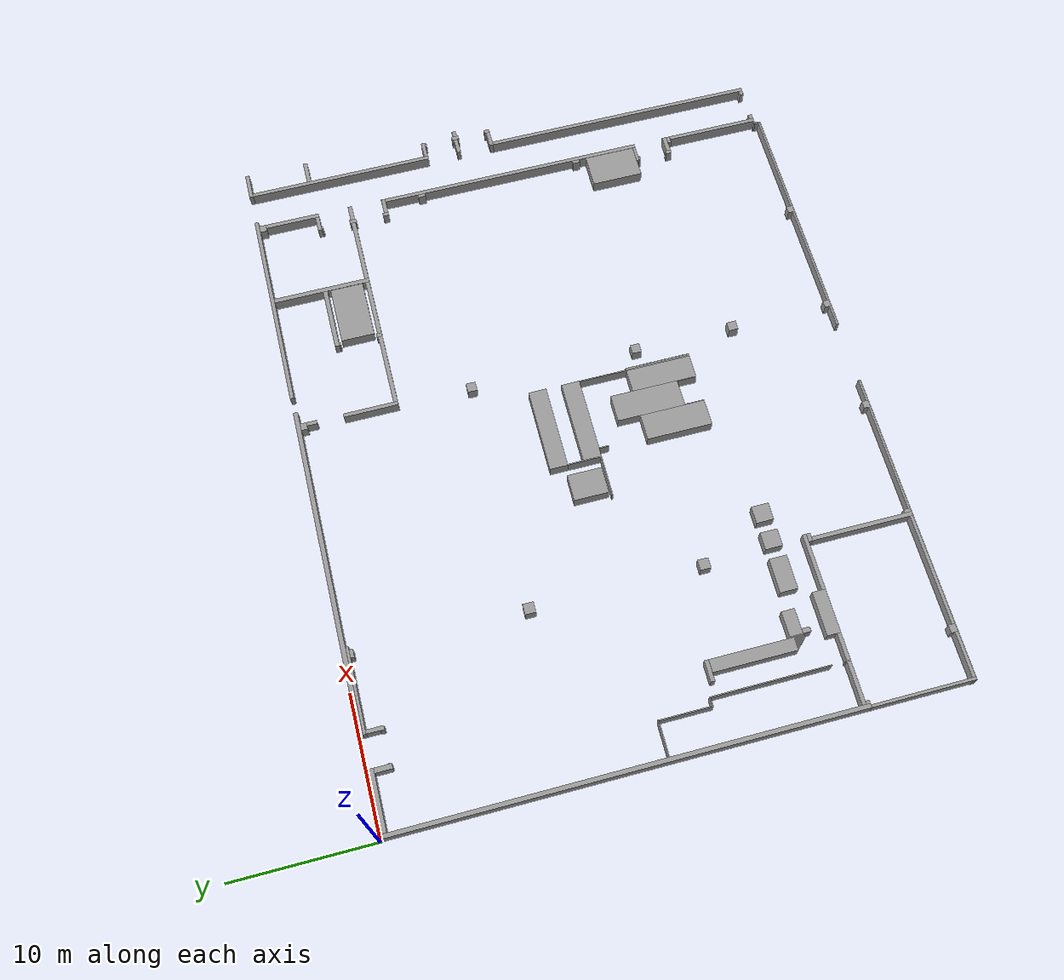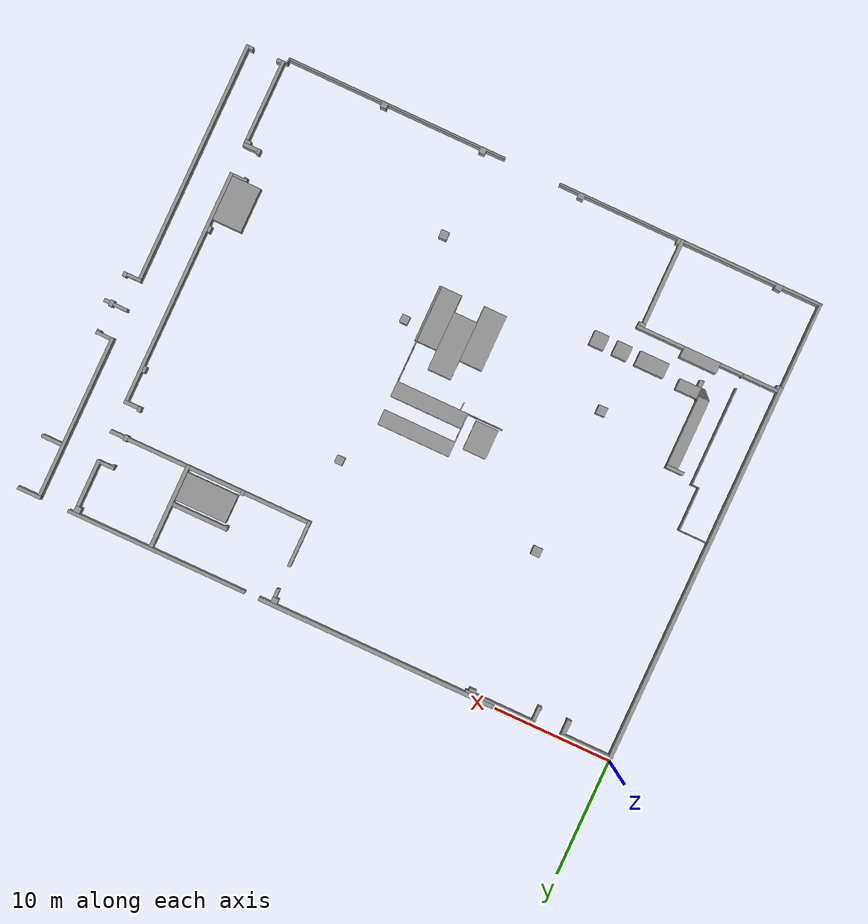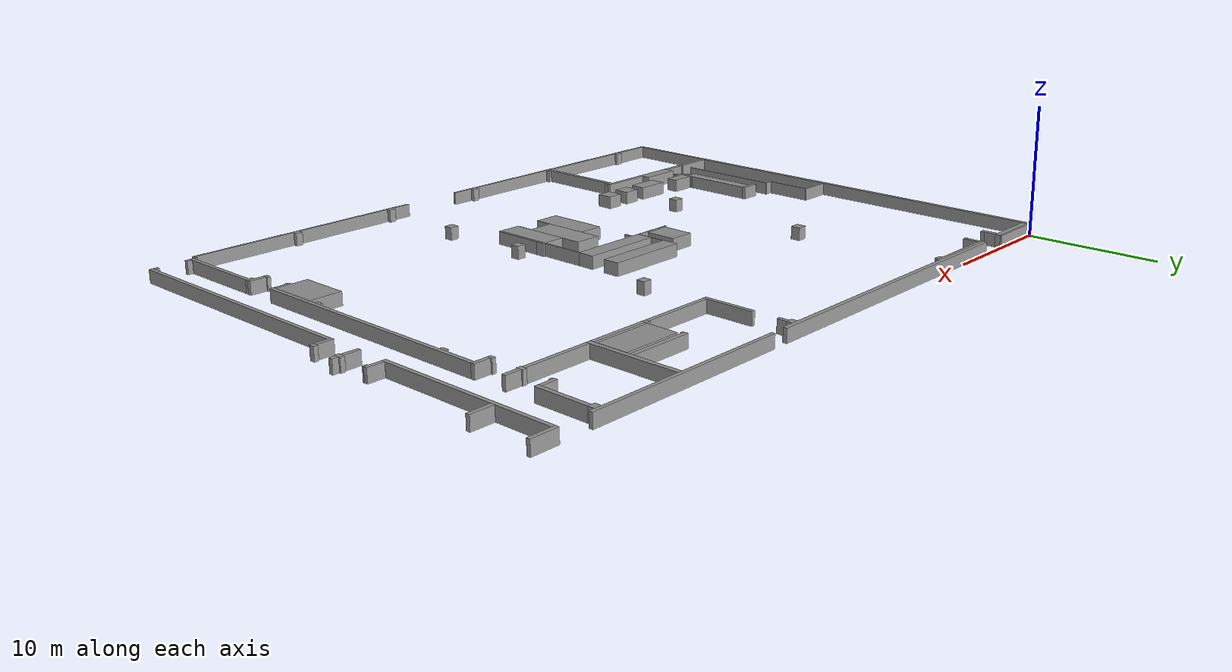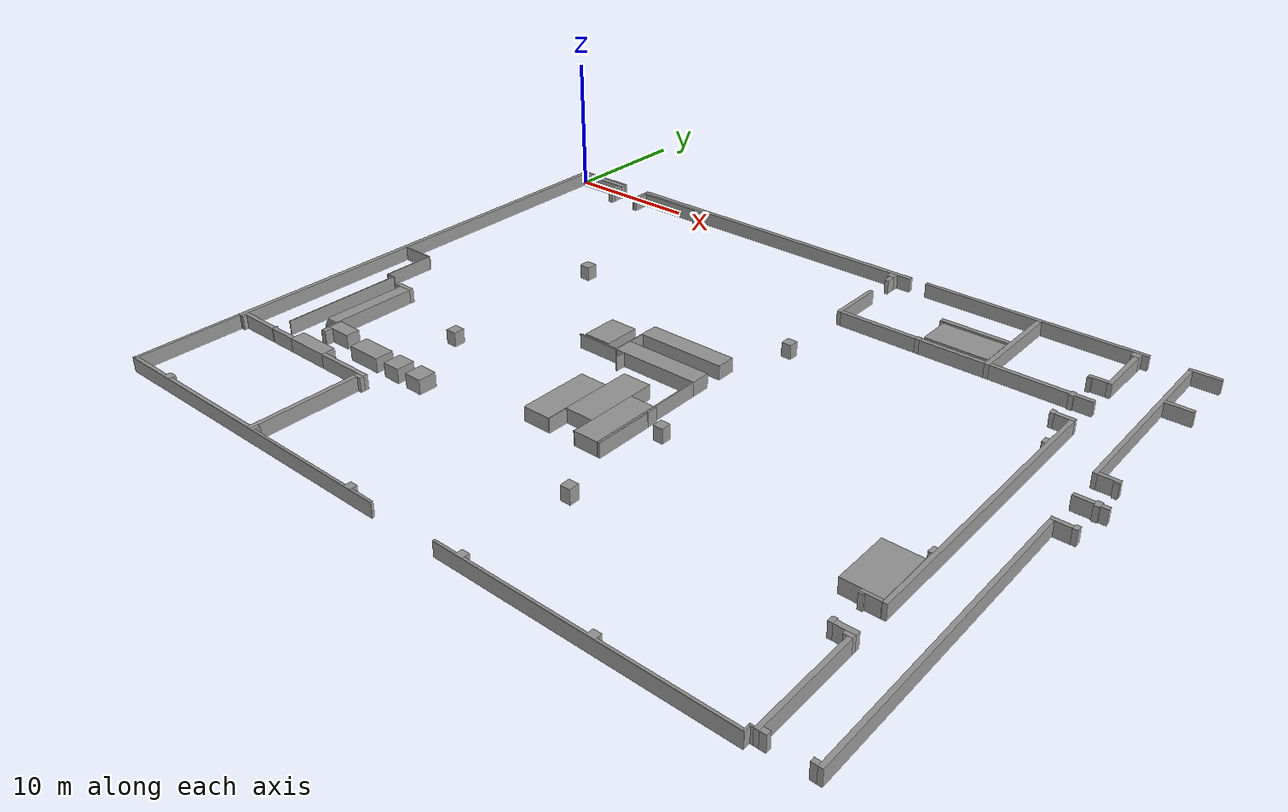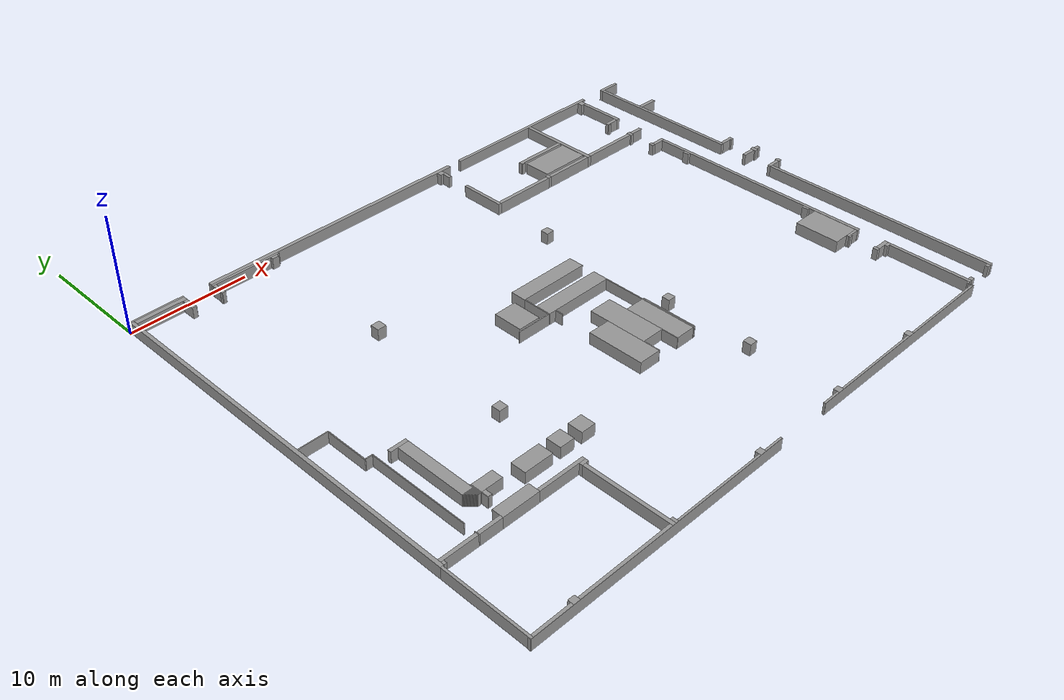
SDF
<?xml version="1.0" ?>
<sdf version="1.4">
  <model name="AdlerErfurtShopLevel1">
    <static>1</static>
    <link name="Wall_0">
      <collision name="Wall_0_Collision">
        <geometry>
          <box>
            <size>4.51915 0.15319 1.00000</size>
          </box>
        </geometry>
        <pose>2.28511 -0.07660 0.50000 0 0 0.00000</pose>
      </collision>
      <visual name="Wall_0_Visual">
        <geometry>
          <box>
            <size>4.51915 0.15319 1.00000</size>
          </box>
        </geometry>
        <material>
          <script>
            <uri>file://media/materials/scripts/gazebo.material</uri>
            <name>Gazebo/Grey</name>
          </script>
        </material>
        <pose>2.28511 -0.07660 0.50000 0 0 0.00000</pose>
      </visual>
    </link>
    <link name="Wall_1">
      <collision name="Wall_1_Collision">
        <geometry>
          <box>
            <size>24.07660 0.33191 1.00000</size>
          </box>
        </geometry>
        <pose>18.85532 -0.16596 0.50000 0 0 0.00000</pose>
      </collision>
      <visual name="Wall_1_Visual">
        <geometry>
          <box>
            <size>24.07660 0.33191 1.00000</size>
          </box>
        </geometry>
        <material>
          <script>
            <uri>file://media/materials/scripts/gazebo.material</uri>
            <name>Gazebo/Grey</name>
          </script>
        </material>
        <pose>18.85532 -0.16596 0.50000 0 0 0.00000</pose>
      </visual>
    </link>
    <link name="Wall_2">
      <collision name="Wall_2_Collision">
        <geometry>
          <box>
            <size>15.49787 0.28085 1.00000</size>
          </box>
        </geometry>
        <pose>39.84255 -0.14043 0.50000 0 0 0.00000</pose>
      </collision>
      <visual name="Wall_2_Visual">
        <geometry>
          <box>
            <size>15.49787 0.28085 1.00000</size>
          </box>
        </geometry>
        <material>
          <script>
            <uri>file://media/materials/scripts/gazebo.material</uri>
            <name>Gazebo/Grey</name>
          </script>
        </material>
        <pose>39.84255 -0.14043 0.50000 0 0 0.00000</pose>
      </visual>
    </link>
    <link name="Wall_3">
      <collision name="Wall_3_Collision">
        <geometry>
          <box>
            <size>2.01702 0.28085 1.00000</size>
          </box>
        </geometry>
        <pose>51.00000 -0.14043 0.50000 0 0 0.00000</pose>
      </collision>
      <visual name="Wall_3_Visual">
        <geometry>
          <box>
            <size>2.01702 0.28085 1.00000</size>
          </box>
        </geometry>
        <material>
          <script>
            <uri>file://media/materials/scripts/gazebo.material</uri>
            <name>Gazebo/Grey</name>
          </script>
        </material>
        <pose>51.00000 -0.14043 0.50000 0 0 0.00000</pose>
      </visual>
    </link>
    <link name="Wall_4">
      <collision name="Wall_4_Collision">
        <geometry>
          <box>
            <size>0.30638 32.73191 1.00000</size>
          </box>
        </geometry>
        <pose>0.17872 -16.51915 0.50000 0 0 0.00000</pose>
      </collision>
      <visual name="Wall_4_Visual">
        <geometry>
          <box>
            <size>0.30638 32.73191 1.00000</size>
          </box>
        </geometry>
        <material>
          <script>
            <uri>file://media/materials/scripts/gazebo.material</uri>
            <name>Gazebo/Grey</name>
          </script>
        </material>
        <pose>0.17872 -16.51915 0.50000 0 0 0.00000</pose>
      </visual>
    </link>
    <link name="Wall_5">
      <collision name="Wall_5_Collision">
        <geometry>
          <box>
            <size>4.18723 0.40851 1.00000</size>
          </box>
        </geometry>
        <pose>2.45106 -0.35745 0.50000 0 0 0.00000</pose>
      </collision>
      <visual name="Wall_5_Visual">
        <geometry>
          <box>
            <size>4.18723 0.40851 1.00000</size>
          </box>
        </geometry>
        <material>
          <script>
            <uri>file://media/materials/scripts/gazebo.material</uri>
            <name>Gazebo/Grey</name>
          </script>
        </material>
        <pose>2.45106 -0.35745 0.50000 0 0 0.00000</pose>
      </visual>
    </link>
    <link name="Wall_6">
      <collision name="Wall_6_Collision">
        <geometry>
          <box>
            <size>0.02553 0.30638 1.00000</size>
          </box>
        </geometry>
        <pose>0.34468 -0.40851 0.50000 0 0 0.00000</pose>
      </collision>
      <visual name="Wall_6_Visual">
        <geometry>
          <box>
            <size>0.02553 0.30638 1.00000</size>
          </box>
        </geometry>
        <material>
          <script>
            <uri>file://media/materials/scripts/gazebo.material</uri>
            <name>Gazebo/Grey</name>
          </script>
        </material>
        <pose>0.34468 -0.40851 0.50000 0 0 0.00000</pose>
      </visual>
    </link>
    <link name="Wall_7">
      <collision name="Wall_7_Collision">
        <geometry>
          <box>
            <size>0.33191 7.17447 1.00000</size>
          </box>
        </geometry>
        <pose>40.40426 -3.86809 0.50000 0 0 0.00000</pose>
      </collision>
      <visual name="Wall_7_Visual">
        <geometry>
          <box>
            <size>0.33191 7.17447 1.00000</size>
          </box>
        </geometry>
        <material>
          <script>
            <uri>file://media/materials/scripts/gazebo.material</uri>
            <name>Gazebo/Grey</name>
          </script>
        </material>
        <pose>40.40426 -3.86809 0.50000 0 0 0.00000</pose>
      </visual>
    </link>
    <link name="Wall_8">
      <collision name="Wall_8_Collision">
        <geometry>
          <box>
            <size>0.53617 0.51064 1.00000</size>
          </box>
        </geometry>
        <pose>46.91489 -0.53617 0.50000 0 0 0.00000</pose>
      </collision>
      <visual name="Wall_8_Visual">
        <geometry>
          <box>
            <size>0.53617 0.51064 1.00000</size>
          </box>
        </geometry>
        <material>
          <script>
            <uri>file://media/materials/scripts/gazebo.material</uri>
            <name>Gazebo/Grey</name>
          </script>
        </material>
        <pose>46.91489 -0.53617 0.50000 0 0 0.00000</pose>
      </visual>
    </link>
    <link name="Wall_9">
      <collision name="Wall_9_Collision">
        <geometry>
          <box>
            <size>0.28085 13.83830 1.00000</size>
          </box>
        </geometry>
        <pose>50.13191 -7.20000 0.50000 0 0 0.00000</pose>
      </collision>
      <visual name="Wall_9_Visual">
        <geometry>
          <box>
            <size>0.28085 13.83830 1.00000</size>
          </box>
        </geometry>
        <material>
          <script>
            <uri>file://media/materials/scripts/gazebo.material</uri>
            <name>Gazebo/Grey</name>
          </script>
        </material>
        <pose>50.13191 -7.20000 0.50000 0 0 0.00000</pose>
      </visual>
    </link>
    <link name="Wall_10">
      <collision name="Wall_10_Collision">
        <geometry>
          <box>
            <size>6.07660 0.20426 1.00000</size>
          </box>
        </geometry>
        <pose>9.85532 -0.43404 0.50000 0 0 0.00000</pose>
      </collision>
      <visual name="Wall_10_Visual">
        <geometry>
          <box>
            <size>6.07660 0.20426 1.00000</size>
          </box>
        </geometry>
        <material>
          <script>
            <uri>file://media/materials/scripts/gazebo.material</uri>
            <name>Gazebo/Grey</name>
          </script>
        </material>
        <pose>9.85532 -0.43404 0.50000 0 0 0.00000</pose>
      </visual>
    </link>
    <link name="Wall_11">
      <collision name="Wall_11_Collision">
        <geometry>
          <box>
            <size>0.53617 0.45957 1.00000</size>
          </box>
        </geometry>
        <pose>29.65532 -0.56170 0.50000 0 0 0.00000</pose>
      </collision>
      <visual name="Wall_11_Visual">
        <geometry>
          <box>
            <size>0.53617 0.45957 1.00000</size>
          </box>
        </geometry>
        <material>
          <script>
            <uri>file://media/materials/scripts/gazebo.material</uri>
            <name>Gazebo/Grey</name>
          </script>
        </material>
        <pose>29.65532 -0.56170 0.50000 0 0 0.00000</pose>
      </visual>
    </link>
    <link name="Wall_12">
      <collision name="Wall_12_Collision">
        <geometry>
          <box>
            <size>0.28085 1.22553 1.00000</size>
          </box>
        </geometry>
        <pose>6.95745 -1.14894 0.50000 0 0 0.00000</pose>
      </collision>
      <visual name="Wall_12_Visual">
        <geometry>
          <box>
            <size>0.28085 1.22553 1.00000</size>
          </box>
        </geometry>
        <material>
          <script>
            <uri>file://media/materials/scripts/gazebo.material</uri>
            <name>Gazebo/Grey</name>
          </script>
        </material>
        <pose>6.95745 -1.14894 0.50000 0 0 0.00000</pose>
      </visual>
    </link>
    <link name="Wall_13">
      <collision name="Wall_13_Collision">
        <geometry>
          <box>
            <size>0.58723 0.25532 1.00000</size>
          </box>
        </geometry>
        <pose>12.37021 -0.66383 0.50000 0 0 0.00000</pose>
      </collision>
      <visual name="Wall_13_Visual">
        <geometry>
          <box>
            <size>0.58723 0.25532 1.00000</size>
          </box>
        </geometry>
        <material>
          <script>
            <uri>file://media/materials/scripts/gazebo.material</uri>
            <name>Gazebo/Grey</name>
          </script>
        </material>
        <pose>12.37021 -0.66383 0.50000 0 0 0.00000</pose>
      </visual>
    </link>
    <link name="Wall_14">
      <collision name="Wall_14_Collision">
        <geometry>
          <box>
            <size>0.35745 1.20000 1.00000</size>
          </box>
        </geometry>
        <pose>4.36596 -1.16170 0.50000 0 0 0.00000</pose>
      </collision>
      <visual name="Wall_14_Visual">
        <geometry>
          <box>
            <size>0.35745 1.20000 1.00000</size>
          </box>
        </geometry>
        <material>
          <script>
            <uri>file://media/materials/scripts/gazebo.material</uri>
            <name>Gazebo/Grey</name>
          </script>
        </material>
        <pose>4.36596 -1.16170 0.50000 0 0 0.00000</pose>
      </visual>
    </link>
    <link name="Wall_15">
      <collision name="Wall_15_Collision">
        <geometry>
          <box>
            <size>0.28085 0.74043 1.00000</size>
          </box>
        </geometry>
        <pose>29.78298 -1.16170 0.50000 0 0 0.00000</pose>
      </collision>
      <visual name="Wall_15_Visual">
        <geometry>
          <box>
            <size>0.28085 0.74043 1.00000</size>
          </box>
        </geometry>
        <material>
          <script>
            <uri>file://media/materials/scripts/gazebo.material</uri>
            <name>Gazebo/Grey</name>
          </script>
        </material>
        <pose>29.78298 -1.16170 0.50000 0 0 0.00000</pose>
      </visual>
    </link>
    <link name="Wall_16">
      <collision name="Wall_16_Collision">
        <geometry>
          <box>
            <size>0.30638 4.05957 1.00000</size>
          </box>
        </geometry>
        <pose>47.02979 -2.82128 0.50000 0 0 0.00000</pose>
      </collision>
      <visual name="Wall_16_Visual">
        <geometry>
          <box>
            <size>0.30638 4.05957 1.00000</size>
          </box>
        </geometry>
        <material>
          <script>
            <uri>file://media/materials/scripts/gazebo.material</uri>
            <name>Gazebo/Grey</name>
          </script>
        </material>
        <pose>47.02979 -2.82128 0.50000 0 0 0.00000</pose>
      </visual>
    </link>
    <link name="Wall_17">
      <collision name="Wall_17_Collision">
        <geometry>
          <box>
            <size>0.02553 0.30638 1.00000</size>
          </box>
        </geometry>
        <pose>4.55745 -1.60851 0.50000 0 0 0.00000</pose>
      </collision>
      <visual name="Wall_17_Visual">
        <geometry>
          <box>
            <size>0.02553 0.30638 1.00000</size>
          </box>
        </geometry>
        <material>
          <script>
            <uri>file://media/materials/scripts/gazebo.material</uri>
            <name>Gazebo/Grey</name>
          </script>
        </material>
        <pose>4.55745 -1.60851 0.50000 0 0 0.00000</pose>
      </visual>
    </link>
    <link name="Wall_18">
      <collision name="Wall_18_Collision">
        <geometry>
          <box>
            <size>0.05106 0.28085 1.00000</size>
          </box>
        </geometry>
        <pose>6.79149 -1.62128 0.50000 0 0 0.00000</pose>
      </collision>
      <visual name="Wall_18_Visual">
        <geometry>
          <box>
            <size>0.05106 0.28085 1.00000</size>
          </box>
        </geometry>
        <material>
          <script>
            <uri>file://media/materials/scripts/gazebo.material</uri>
            <name>Gazebo/Grey</name>
          </script>
        </material>
        <pose>6.79149 -1.62128 0.50000 0 0 0.00000</pose>
      </visual>
    </link>
    <link name="Wall_19">
      <collision name="Wall_19_Collision">
        <geometry>
          <box>
            <size>0.28085 3.98298 1.00000</size>
          </box>
        </geometry>
        <pose>29.78298 -5.46383 0.50000 0 0 0.00000</pose>
      </collision>
      <visual name="Wall_19_Visual">
        <geometry>
          <box>
            <size>0.28085 3.98298 1.00000</size>
          </box>
        </geometry>
        <material>
          <script>
            <uri>file://media/materials/scripts/gazebo.material</uri>
            <name>Gazebo/Grey</name>
          </script>
        </material>
        <pose>29.78298 -5.46383 0.50000 0 0 0.00000</pose>
      </visual>
    </link>
    <link name="Wall_20">
      <collision name="Wall_20_Collision">
        <geometry>
          <box>
            <size>4.77447 0.33191 1.00000</size>
          </box>
        </geometry>
        <pose>37.85106 -4.09787 0.50000 0 0 0.00000</pose>
      </collision>
      <visual name="Wall_20_Visual">
        <geometry>
          <box>
            <size>4.77447 0.33191 1.00000</size>
          </box>
        </geometry>
        <material>
          <script>
            <uri>file://media/materials/scripts/gazebo.material</uri>
            <name>Gazebo/Grey</name>
          </script>
        </material>
        <pose>37.85106 -4.09787 0.50000 0 0 0.00000</pose>
      </visual>
    </link>
    <link name="Wall_21">
      <collision name="Wall_21_Collision">
        <geometry>
          <box>
            <size>0.28085 0.10213 1.00000</size>
          </box>
        </geometry>
        <pose>35.60426 -4.31489 0.50000 0 0 0.00000</pose>
      </collision>
      <visual name="Wall_21_Visual">
        <geometry>
          <box>
            <size>0.28085 0.10213 1.00000</size>
          </box>
        </geometry>
        <material>
          <script>
            <uri>file://media/materials/scripts/gazebo.material</uri>
            <name>Gazebo/Grey</name>
          </script>
        </material>
        <pose>35.60426 -4.31489 0.50000 0 0 0.00000</pose>
      </visual>
    </link>
    <link name="Wall_22">
      <collision name="Wall_22_Collision">
        <geometry>
          <box>
            <size>4.41702 2.42553 1.00000</size>
          </box>
        </geometry>
        <pose>38.00426 -5.70638 0.50000 0 0 0.00000</pose>
      </collision>
      <visual name="Wall_22_Visual">
        <geometry>
          <box>
            <size>4.41702 2.42553 1.00000</size>
          </box>
        </geometry>
        <material>
          <script>
            <uri>file://media/materials/scripts/gazebo.material</uri>
            <name>Gazebo/Grey</name>
          </script>
        </material>
        <pose>38.00426 -5.70638 0.50000 0 0 0.00000</pose>
      </visual>
    </link>
    <link name="Wall_23">
      <collision name="Wall_23_Collision">
        <geometry>
          <box>
            <size>1.73617 0.30638 1.00000</size>
          </box>
        </geometry>
        <pose>51.14043 -4.69787 0.50000 0 0 0.00000</pose>
      </collision>
      <visual name="Wall_23_Visual">
        <geometry>
          <box>
            <size>1.73617 0.30638 1.00000</size>
          </box>
        </geometry>
        <material>
          <script>
            <uri>file://media/materials/scripts/gazebo.material</uri>
            <name>Gazebo/Grey</name>
          </script>
        </material>
        <pose>51.14043 -4.69787 0.50000 0 0 0.00000</pose>
      </visual>
    </link>
    <link name="Wall_24">
      <collision name="Wall_24_Collision">
        <geometry>
          <box>
            <size>1.20000 0.28085 1.00000</size>
          </box>
        </geometry>
        <pose>46.27660 -4.71064 0.50000 0 0 0.00000</pose>
      </collision>
      <visual name="Wall_24_Visual">
        <geometry>
          <box>
            <size>1.20000 0.28085 1.00000</size>
          </box>
        </geometry>
        <material>
          <script>
            <uri>file://media/materials/scripts/gazebo.material</uri>
            <name>Gazebo/Grey</name>
          </script>
        </material>
        <pose>46.27660 -4.71064 0.50000 0 0 0.00000</pose>
      </visual>
    </link>
    <link name="Wall_25">
      <collision name="Wall_25_Collision">
        <geometry>
          <box>
            <size>0.28085 0.12766 1.00000</size>
          </box>
        </geometry>
        <pose>45.81702 -4.91489 0.50000 0 0 0.00000</pose>
      </collision>
      <visual name="Wall_25_Visual">
        <geometry>
          <box>
            <size>0.28085 0.12766 1.00000</size>
          </box>
        </geometry>
        <material>
          <script>
            <uri>file://media/materials/scripts/gazebo.material</uri>
            <name>Gazebo/Grey</name>
          </script>
        </material>
        <pose>45.81702 -4.91489 0.50000 0 0 0.00000</pose>
      </visual>
    </link>
    <link name="Wall_26">
      <collision name="Wall_26_Collision">
        <geometry>
          <box>
            <size>0.30638 0.40851 1.00000</size>
          </box>
        </geometry>
        <pose>35.59149 -7.25106 0.50000 0 0 0.00000</pose>
      </collision>
      <visual name="Wall_26_Visual">
        <geometry>
          <box>
            <size>0.30638 0.40851 1.00000</size>
          </box>
        </geometry>
        <material>
          <script>
            <uri>file://media/materials/scripts/gazebo.material</uri>
            <name>Gazebo/Grey</name>
          </script>
        </material>
        <pose>35.59149 -7.25106 0.50000 0 0 0.00000</pose>
      </visual>
    </link>
    <link name="Wall_27">
      <collision name="Wall_27_Collision">
        <geometry>
          <box>
            <size>0.30638 0.51064 1.00000</size>
          </box>
        </geometry>
        <pose>45.82979 -7.30213 0.50000 0 0 0.00000</pose>
      </collision>
      <visual name="Wall_27_Visual">
        <geometry>
          <box>
            <size>0.30638 0.51064 1.00000</size>
          </box>
        </geometry>
        <material>
          <script>
            <uri>file://media/materials/scripts/gazebo.material</uri>
            <name>Gazebo/Grey</name>
          </script>
        </material>
        <pose>45.82979 -7.30213 0.50000 0 0 0.00000</pose>
      </visual>
    </link>
    <link name="Wall_28">
      <collision name="Wall_28_Collision">
        <geometry>
          <box>
            <size>5.51489 0.30638 1.00000</size>
          </box>
        </geometry>
        <pose>32.68085 -7.30213 0.50000 0 0 0.00000</pose>
      </collision>
      <visual name="Wall_28_Visual">
        <geometry>
          <box>
            <size>5.51489 0.30638 1.00000</size>
          </box>
        </geometry>
        <material>
          <script>
            <uri>file://media/materials/scripts/gazebo.material</uri>
            <name>Gazebo/Grey</name>
          </script>
        </material>
        <pose>32.68085 -7.30213 0.50000 0 0 0.00000</pose>
      </visual>
    </link>
    <link name="Wall_29">
      <collision name="Wall_29_Collision">
        <geometry>
          <box>
            <size>4.49362 0.30638 1.00000</size>
          </box>
        </geometry>
        <pose>37.99149 -7.30213 0.50000 0 0 0.00000</pose>
      </collision>
      <visual name="Wall_29_Visual">
        <geometry>
          <box>
            <size>4.49362 0.30638 1.00000</size>
          </box>
        </geometry>
        <material>
          <script>
            <uri>file://media/materials/scripts/gazebo.material</uri>
            <name>Gazebo/Grey</name>
          </script>
        </material>
        <pose>37.99149 -7.30213 0.50000 0 0 0.00000</pose>
      </visual>
    </link>
    <link name="Wall_30">
      <collision name="Wall_30_Collision">
        <geometry>
          <box>
            <size>5.10638 0.30638 1.00000</size>
          </box>
        </geometry>
        <pose>43.12340 -7.30213 0.50000 0 0 0.00000</pose>
      </collision>
      <visual name="Wall_30_Visual">
        <geometry>
          <box>
            <size>5.10638 0.30638 1.00000</size>
          </box>
        </geometry>
        <material>
          <script>
            <uri>file://media/materials/scripts/gazebo.material</uri>
            <name>Gazebo/Grey</name>
          </script>
        </material>
        <pose>43.12340 -7.30213 0.50000 0 0 0.00000</pose>
      </visual>
    </link>
    <link name="Wall_31">
      <collision name="Wall_31_Collision">
        <geometry>
          <box>
            <size>1.20000 0.30638 1.00000</size>
          </box>
        </geometry>
        <pose>46.58298 -7.30213 0.50000 0 0 0.00000</pose>
      </collision>
      <visual name="Wall_31_Visual">
        <geometry>
          <box>
            <size>1.20000 0.30638 1.00000</size>
          </box>
        </geometry>
        <material>
          <script>
            <uri>file://media/materials/scripts/gazebo.material</uri>
            <name>Gazebo/Grey</name>
          </script>
        </material>
        <pose>46.58298 -7.30213 0.50000 0 0 0.00000</pose>
      </visual>
    </link>
    <link name="Wall_32">
      <collision name="Wall_32_Collision">
        <geometry>
          <box>
            <size>0.28085 0.43404 1.00000</size>
          </box>
        </geometry>
        <pose>45.81702 -9.84255 0.50000 0 0 0.00000</pose>
      </collision>
      <visual name="Wall_32_Visual">
        <geometry>
          <box>
            <size>0.28085 0.43404 1.00000</size>
          </box>
        </geometry>
        <material>
          <script>
            <uri>file://media/materials/scripts/gazebo.material</uri>
            <name>Gazebo/Grey</name>
          </script>
        </material>
        <pose>45.81702 -9.84255 0.50000 0 0 0.00000</pose>
      </visual>
    </link>
    <link name="Wall_33">
      <collision name="Wall_33_Collision">
        <geometry>
          <box>
            <size>1.22553 0.30638 1.00000</size>
          </box>
        </geometry>
        <pose>46.57021 -9.90638 0.50000 0 0 0.00000</pose>
      </collision>
      <visual name="Wall_33_Visual">
        <geometry>
          <box>
            <size>1.22553 0.30638 1.00000</size>
          </box>
        </geometry>
        <material>
          <script>
            <uri>file://media/materials/scripts/gazebo.material</uri>
            <name>Gazebo/Grey</name>
          </script>
        </material>
        <pose>46.57021 -9.90638 0.50000 0 0 0.00000</pose>
      </visual>
    </link>
    <link name="Wall_34">
      <collision name="Wall_34_Collision">
        <geometry>
          <box>
            <size>0.28085 19.94043 1.00000</size>
          </box>
        </geometry>
        <pose>47.04255 -20.02979 0.50000 0 0 0.00000</pose>
      </collision>
      <visual name="Wall_34_Visual">
        <geometry>
          <box>
            <size>0.28085 19.94043 1.00000</size>
          </box>
        </geometry>
        <material>
          <script>
            <uri>file://media/materials/scripts/gazebo.material</uri>
            <name>Gazebo/Grey</name>
          </script>
        </material>
        <pose>47.04255 -20.02979 0.50000 0 0 0.00000</pose>
      </visual>
    </link>
    <link name="Wall_35">
      <collision name="Wall_35_Collision">
        <geometry>
          <box>
            <size>0.76596 0.76596 1.00000</size>
          </box>
        </geometry>
        <pose>12.38298 -12.84255 0.50000 0 0 0.00000</pose>
      </collision>
      <visual name="Wall_35_Visual">
        <geometry>
          <box>
            <size>0.76596 0.76596 1.00000</size>
          </box>
        </geometry>
        <material>
          <script>
            <uri>file://media/materials/scripts/gazebo.material</uri>
            <name>Gazebo/Grey</name>
          </script>
        </material>
        <pose>12.38298 -12.84255 0.50000 0 0 0.00000</pose>
      </visual>
    </link>
    <link name="Wall_36">
      <collision name="Wall_36_Collision">
        <geometry>
          <box>
            <size>0.68936 0.68936 1.00000</size>
          </box>
        </geometry>
        <pose>29.65532 -12.85532 0.50000 0 0 0.00000</pose>
      </collision>
      <visual name="Wall_36_Visual">
        <geometry>
          <box>
            <size>0.68936 0.68936 1.00000</size>
          </box>
        </geometry>
        <material>
          <script>
            <uri>file://media/materials/scripts/gazebo.material</uri>
            <name>Gazebo/Grey</name>
          </script>
        </material>
        <pose>29.65532 -12.85532 0.50000 0 0 0.00000</pose>
      </visual>
    </link>
    <link name="Wall_37">
      <collision name="Wall_37_Collision">
        <geometry>
          <box>
            <size>0.25532 0.56170 1.00000</size>
          </box>
        </geometry>
        <pose>46.77447 -12.86809 0.50000 0 0 0.00000</pose>
      </collision>
      <visual name="Wall_37_Visual">
        <geometry>
          <box>
            <size>0.25532 0.56170 1.00000</size>
          </box>
        </geometry>
        <material>
          <script>
            <uri>file://media/materials/scripts/gazebo.material</uri>
            <name>Gazebo/Grey</name>
          </script>
        </material>
        <pose>46.77447 -12.86809 0.50000 0 0 0.00000</pose>
      </visual>
    </link>
    <link name="Wall_38">
      <collision name="Wall_38_Collision">
        <geometry>
          <box>
            <size>1.25106 0.28085 1.00000</size>
          </box>
        </geometry>
        <pose>50.89787 -13.97872 0.50000 0 0 0.00000</pose>
      </collision>
      <visual name="Wall_38_Visual">
        <geometry>
          <box>
            <size>1.25106 0.28085 1.00000</size>
          </box>
        </geometry>
        <material>
          <script>
            <uri>file://media/materials/scripts/gazebo.material</uri>
            <name>Gazebo/Grey</name>
          </script>
        </material>
        <pose>50.89787 -13.97872 0.50000 0 0 0.00000</pose>
      </visual>
    </link>
    <link name="Wall_39">
      <collision name="Wall_39_Collision">
        <geometry>
          <box>
            <size>0.33191 0.12766 1.00000</size>
          </box>
        </geometry>
        <pose>51.35745 -14.18298 0.50000 0 0 0.00000</pose>
      </collision>
      <visual name="Wall_39_Visual">
        <geometry>
          <box>
            <size>0.33191 0.12766 1.00000</size>
          </box>
        </geometry>
        <material>
          <script>
            <uri>file://media/materials/scripts/gazebo.material</uri>
            <name>Gazebo/Grey</name>
          </script>
        </material>
        <pose>51.35745 -14.18298 0.50000 0 0 0.00000</pose>
      </visual>
    </link>
    <link name="Wall_40">
      <collision name="Wall_40_Collision">
        <geometry>
          <box>
            <size>0.33191 0.53617 1.00000</size>
          </box>
        </geometry>
        <pose>51.38298 -16.55745 0.50000 0 0 0.00000</pose>
      </collision>
      <visual name="Wall_40_Visual">
        <geometry>
          <box>
            <size>0.33191 0.53617 1.00000</size>
          </box>
        </geometry>
        <material>
          <script>
            <uri>file://media/materials/scripts/gazebo.material</uri>
            <name>Gazebo/Grey</name>
          </script>
        </material>
        <pose>51.38298 -16.55745 0.50000 0 0 0.00000</pose>
      </visual>
    </link>
    <link name="Wall_41">
      <collision name="Wall_41_Collision">
        <geometry>
          <box>
            <size>1.22553 0.28085 1.00000</size>
          </box>
        </geometry>
        <pose>50.60426 -16.55745 0.50000 0 0 0.00000</pose>
      </collision>
      <visual name="Wall_41_Visual">
        <geometry>
          <box>
            <size>1.22553 0.28085 1.00000</size>
          </box>
        </geometry>
        <material>
          <script>
            <uri>file://media/materials/scripts/gazebo.material</uri>
            <name>Gazebo/Grey</name>
          </script>
        </material>
        <pose>50.60426 -16.55745 0.50000 0 0 0.00000</pose>
      </visual>
    </link>
    <link name="Wall_42">
      <collision name="Wall_42_Collision">
        <geometry>
          <box>
            <size>0.45957 0.30638 1.00000</size>
          </box>
        </geometry>
        <pose>51.77872 -16.57021 0.50000 0 0 0.00000</pose>
      </collision>
      <visual name="Wall_42_Visual">
        <geometry>
          <box>
            <size>0.45957 0.30638 1.00000</size>
          </box>
        </geometry>
        <material>
          <script>
            <uri>file://media/materials/scripts/gazebo.material</uri>
            <name>Gazebo/Grey</name>
          </script>
        </material>
        <pose>51.77872 -16.57021 0.50000 0 0 0.00000</pose>
      </visual>
    </link>
    <link name="Wall_43">
      <collision name="Wall_43_Collision">
        <geometry>
          <box>
            <size>6.22979 1.30213 1.00000</size>
          </box>
        </geometry>
        <pose>25.02128 -17.37447 0.50000 0 0 0.00000</pose>
      </collision>
      <visual name="Wall_43_Visual">
        <geometry>
          <box>
            <size>6.22979 1.30213 1.00000</size>
          </box>
        </geometry>
        <material>
          <script>
            <uri>file://media/materials/scripts/gazebo.material</uri>
            <name>Gazebo/Grey</name>
          </script>
        </material>
        <pose>25.02128 -17.37447 0.50000 0 0 0.00000</pose>
      </visual>
    </link>
    <link name="Wall_44">
      <collision name="Wall_44_Collision">
        <geometry>
          <box>
            <size>1.96596 2.50213 1.00000</size>
          </box>
        </geometry>
        <pose>20.15745 -19.02128 0.50000 0 0 0.00000</pose>
      </collision>
      <visual name="Wall_44_Visual">
        <geometry>
          <box>
            <size>1.96596 2.50213 1.00000</size>
          </box>
        </geometry>
        <material>
          <script>
            <uri>file://media/materials/scripts/gazebo.material</uri>
            <name>Gazebo/Grey</name>
          </script>
        </material>
        <pose>20.15745 -19.02128 0.50000 0 0 0.00000</pose>
      </visual>
    </link>
    <link name="Wall_45">
      <collision name="Wall_45_Collision">
        <geometry>
          <box>
            <size>0.07660 2.47660 1.00000</size>
          </box>
        </geometry>
        <pose>21.94468 -19.26383 0.50000 0 0 0.00000</pose>
      </collision>
      <visual name="Wall_45_Visual">
        <geometry>
          <box>
            <size>0.07660 2.47660 1.00000</size>
          </box>
        </geometry>
        <material>
          <script>
            <uri>file://media/materials/scripts/gazebo.material</uri>
            <name>Gazebo/Grey</name>
          </script>
        </material>
        <pose>21.94468 -19.26383 0.50000 0 0 0.00000</pose>
      </visual>
    </link>
    <link name="Wall_46">
      <collision name="Wall_46_Collision">
        <geometry>
          <box>
            <size>0.30638 0.40851 1.00000</size>
          </box>
        </geometry>
        <pose>51.37021 -19.09787 0.50000 0 0 0.00000</pose>
      </collision>
      <visual name="Wall_46_Visual">
        <geometry>
          <box>
            <size>0.30638 0.40851 1.00000</size>
          </box>
        </geometry>
        <material>
          <script>
            <uri>file://media/materials/scripts/gazebo.material</uri>
            <name>Gazebo/Grey</name>
          </script>
        </material>
        <pose>51.37021 -19.09787 0.50000 0 0 0.00000</pose>
      </visual>
    </link>
    <link name="Wall_47">
      <collision name="Wall_47_Collision">
        <geometry>
          <box>
            <size>1.22553 0.28085 1.00000</size>
          </box>
        </geometry>
        <pose>50.60426 -19.16170 0.50000 0 0 0.00000</pose>
      </collision>
      <visual name="Wall_47_Visual">
        <geometry>
          <box>
            <size>1.22553 0.28085 1.00000</size>
          </box>
        </geometry>
        <material>
          <script>
            <uri>file://media/materials/scripts/gazebo.material</uri>
            <name>Gazebo/Grey</name>
          </script>
        </material>
        <pose>50.60426 -19.16170 0.50000 0 0 0.00000</pose>
      </visual>
    </link>
    <link name="Wall_48">
      <collision name="Wall_48_Collision">
        <geometry>
          <box>
            <size>2.50213 0.07660 1.00000</size>
          </box>
        </geometry>
        <pose>1.58298 -19.13617 0.50000 0 0 0.00000</pose>
      </collision>
      <visual name="Wall_48_Visual">
        <geometry>
          <box>
            <size>2.50213 0.07660 1.00000</size>
          </box>
        </geometry>
        <material>
          <script>
            <uri>file://media/materials/scripts/gazebo.material</uri>
            <name>Gazebo/Grey</name>
          </script>
        </material>
        <pose>1.58298 -19.13617 0.50000 0 0 0.00000</pose>
      </visual>
    </link>
    <link name="Wall_49">
      <collision name="Wall_49_Collision">
        <geometry>
          <box>
            <size>0.07660 3.70213 1.00000</size>
          </box>
        </geometry>
        <pose>2.79574 -21.02553 0.50000 0 0 0.00000</pose>
      </collision>
      <visual name="Wall_49_Visual">
        <geometry>
          <box>
            <size>0.07660 3.70213 1.00000</size>
          </box>
        </geometry>
        <material>
          <script>
            <uri>file://media/materials/scripts/gazebo.material</uri>
            <name>Gazebo/Grey</name>
          </script>
        </material>
        <pose>2.79574 -21.02553 0.50000 0 0 0.00000</pose>
      </visual>
    </link>
    <link name="Wall_50">
      <collision name="Wall_50_Collision">
        <geometry>
          <box>
            <size>6.15319 1.32766 1.00000</size>
          </box>
        </geometry>
        <pose>25.05957 -19.83830 0.50000 0 0 0.00000</pose>
      </collision>
      <visual name="Wall_50_Visual">
        <geometry>
          <box>
            <size>6.15319 1.32766 1.00000</size>
          </box>
        </geometry>
        <material>
          <script>
            <uri>file://media/materials/scripts/gazebo.material</uri>
            <name>Gazebo/Grey</name>
          </script>
        </material>
        <pose>25.05957 -19.83830 0.50000 0 0 0.00000</pose>
      </visual>
    </link>
    <link name="Wall_51">
      <collision name="Wall_51_Collision">
        <geometry>
          <box>
            <size>0.28085 20.47660 1.00000</size>
          </box>
        </geometry>
        <pose>50.13191 -29.54043 0.50000 0 0 0.00000</pose>
      </collision>
      <visual name="Wall_51_Visual">
        <geometry>
          <box>
            <size>0.28085 20.47660 1.00000</size>
          </box>
        </geometry>
        <material>
          <script>
            <uri>file://media/materials/scripts/gazebo.material</uri>
            <name>Gazebo/Grey</name>
          </script>
        </material>
        <pose>50.13191 -29.54043 0.50000 0 0 0.00000</pose>
      </visual>
    </link>
    <link name="Wall_52">
      <collision name="Wall_52_Collision">
        <geometry>
          <box>
            <size>2.98723 0.07660 1.00000</size>
          </box>
        </geometry>
        <pose>20.41277 -20.46383 0.50000 0 0 0.00000</pose>
      </collision>
      <visual name="Wall_52_Visual">
        <geometry>
          <box>
            <size>2.98723 0.07660 1.00000</size>
          </box>
        </geometry>
        <material>
          <script>
            <uri>file://media/materials/scripts/gazebo.material</uri>
            <name>Gazebo/Grey</name>
          </script>
        </material>
        <pose>20.41277 -20.46383 0.50000 0 0 0.00000</pose>
      </visual>
    </link>
    <link name="Wall_53">
      <collision name="Wall_53_Collision">
        <geometry>
          <box>
            <size>0.07660 0.68936 1.00000</size>
          </box>
        </geometry>
        <pose>22.60851 -20.84681 0.50000 0 0 0.00000</pose>
      </collision>
      <visual name="Wall_53_Visual">
        <geometry>
          <box>
            <size>0.07660 0.68936 1.00000</size>
          </box>
        </geometry>
        <material>
          <script>
            <uri>file://media/materials/scripts/gazebo.material</uri>
            <name>Gazebo/Grey</name>
          </script>
        </material>
        <pose>22.60851 -20.84681 0.50000 0 0 0.00000</pose>
      </visual>
    </link>
    <link name="Wall_54">
      <collision name="Wall_54_Collision">
        <geometry>
          <box>
            <size>0.07660 8.29787 1.00000</size>
          </box>
        </geometry>
        <pose>28.09787 -24.65106 0.50000 0 0 0.00000</pose>
      </collision>
      <visual name="Wall_54_Visual">
        <geometry>
          <box>
            <size>0.07660 8.29787 1.00000</size>
          </box>
        </geometry>
        <material>
          <script>
            <uri>file://media/materials/scripts/gazebo.material</uri>
            <name>Gazebo/Grey</name>
          </script>
        </material>
        <pose>28.09787 -24.65106 0.50000 0 0 0.00000</pose>
      </visual>
    </link>
    <link name="Wall_55">
      <collision name="Wall_55_Collision">
        <geometry>
          <box>
            <size>2.01702 5.00426 1.00000</size>
          </box>
        </geometry>
        <pose>25.34043 -24.86809 0.50000 0 0 0.00000</pose>
      </collision>
      <visual name="Wall_55_Visual">
        <geometry>
          <box>
            <size>2.01702 5.00426 1.00000</size>
          </box>
        </geometry>
        <material>
          <script>
            <uri>file://media/materials/scripts/gazebo.material</uri>
            <name>Gazebo/Grey</name>
          </script>
        </material>
        <pose>25.34043 -24.86809 0.50000 0 0 0.00000</pose>
      </visual>
    </link>
    <link name="Wall_56">
      <collision name="Wall_56_Collision">
        <geometry>
          <box>
            <size>0.61277 0.07660 1.00000</size>
          </box>
        </geometry>
        <pose>3.14043 -22.83830 0.50000 0 0 0.00000</pose>
      </collision>
      <visual name="Wall_56_Visual">
        <geometry>
          <box>
            <size>0.61277 0.07660 1.00000</size>
          </box>
        </geometry>
        <material>
          <script>
            <uri>file://media/materials/scripts/gazebo.material</uri>
            <name>Gazebo/Grey</name>
          </script>
        </material>
        <pose>3.14043 -22.83830 0.50000 0 0 0.00000</pose>
      </visual>
    </link>
    <link name="Wall_57">
      <collision name="Wall_57_Collision">
        <geometry>
          <box>
            <size>0.07660 8.42553 1.00000</size>
          </box>
        </geometry>
        <pose>3.40851 -27.08936 0.50000 0 0 0.00000</pose>
      </collision>
      <visual name="Wall_57_Visual">
        <geometry>
          <box>
            <size>0.07660 8.42553 1.00000</size>
          </box>
        </geometry>
        <material>
          <script>
            <uri>file://media/materials/scripts/gazebo.material</uri>
            <name>Gazebo/Grey</name>
          </script>
        </material>
        <pose>3.40851 -27.08936 0.50000 0 0 0.00000</pose>
      </visual>
    </link>
    <link name="Wall_58">
      <collision name="Wall_58_Collision">
        <geometry>
          <box>
            <size>1.50638 0.30638 1.00000</size>
          </box>
        </geometry>
        <pose>5.11915 -23.33617 0.50000 0 0 0.00000</pose>
      </collision>
      <visual name="Wall_58_Visual">
        <geometry>
          <box>
            <size>1.50638 0.30638 1.00000</size>
          </box>
        </geometry>
        <material>
          <script>
            <uri>file://media/materials/scripts/gazebo.material</uri>
            <name>Gazebo/Grey</name>
          </script>
        </material>
        <pose>5.11915 -23.33617 0.50000 0 0 0.00000</pose>
      </visual>
    </link>
    <link name="Wall_59">
      <collision name="Wall_59_Collision">
        <geometry>
          <box>
            <size>0.91915 5.97447 1.00000</size>
          </box>
        </geometry>
        <pose>5.41277 -26.47660 0.50000 0 0 0.00000</pose>
      </collision>
      <visual name="Wall_59_Visual">
        <geometry>
          <box>
            <size>0.91915 5.97447 1.00000</size>
          </box>
        </geometry>
        <material>
          <script>
            <uri>file://media/materials/scripts/gazebo.material</uri>
            <name>Gazebo/Grey</name>
          </script>
        </material>
        <pose>5.41277 -26.47660 0.50000 0 0 0.00000</pose>
      </visual>
    </link>
    <link name="Wall_60">
      <collision name="Wall_60_Collision">
        <geometry>
          <box>
            <size>1.94043 4.77447 1.00000</size>
          </box>
        </geometry>
        <pose>23.36170 -26.41277 0.50000 0 0 0.00000</pose>
      </collision>
      <visual name="Wall_60_Visual">
        <geometry>
          <box>
            <size>1.94043 4.77447 1.00000</size>
          </box>
        </geometry>
        <material>
          <script>
            <uri>file://media/materials/scripts/gazebo.material</uri>
            <name>Gazebo/Grey</name>
          </script>
        </material>
        <pose>23.36170 -26.41277 0.50000 0 0 0.00000</pose>
      </visual>
    </link>
    <link name="Wall_61">
      <collision name="Wall_61_Collision">
        <geometry>
          <box>
            <size>1.71064 4.77447 1.00000</size>
          </box>
        </geometry>
        <pose>27.20426 -26.41277 0.50000 0 0 0.00000</pose>
      </collision>
      <visual name="Wall_61_Visual">
        <geometry>
          <box>
            <size>1.71064 4.77447 1.00000</size>
          </box>
        </geometry>
        <material>
          <script>
            <uri>file://media/materials/scripts/gazebo.material</uri>
            <name>Gazebo/Grey</name>
          </script>
        </material>
        <pose>27.20426 -26.41277 0.50000 0 0 0.00000</pose>
      </visual>
    </link>
    <link name="Wall_62">
      <collision name="Wall_62_Collision">
        <geometry>
          <box>
            <size>0.12766 0.71489 1.00000</size>
          </box>
        </geometry>
        <pose>28.20000 -24.38298 0.50000 0 0 0.00000</pose>
      </collision>
      <visual name="Wall_62_Visual">
        <geometry>
          <box>
            <size>0.12766 0.71489 1.00000</size>
          </box>
        </geometry>
        <material>
          <script>
            <uri>file://media/materials/scripts/gazebo.material</uri>
            <name>Gazebo/Grey</name>
          </script>
        </material>
        <pose>28.20000 -24.38298 0.50000 0 0 0.00000</pose>
      </visual>
    </link>
    <link name="Wall_63">
      <collision name="Wall_63_Collision">
        <geometry>
          <box>
            <size>0.10213 4.05957 1.00000</size>
          </box>
        </geometry>
        <pose>28.18723 -26.77021 0.50000 0 0 0.00000</pose>
      </collision>
      <visual name="Wall_63_Visual">
        <geometry>
          <box>
            <size>0.10213 4.05957 1.00000</size>
          </box>
        </geometry>
        <material>
          <script>
            <uri>file://media/materials/scripts/gazebo.material</uri>
            <name>Gazebo/Grey</name>
          </script>
        </material>
        <pose>28.18723 -26.77021 0.50000 0 0 0.00000</pose>
      </visual>
    </link>
    <link name="Wall_64">
      <collision name="Wall_64_Collision">
        <geometry>
          <box>
            <size>0.76596 0.76596 1.00000</size>
          </box>
        </geometry>
        <pose>12.38298 -25.17447 0.50000 0 0 0.00000</pose>
      </collision>
      <visual name="Wall_64_Visual">
        <geometry>
          <box>
            <size>0.76596 0.76596 1.00000</size>
          </box>
        </geometry>
        <material>
          <script>
            <uri>file://media/materials/scripts/gazebo.material</uri>
            <name>Gazebo/Grey</name>
          </script>
        </material>
        <pose>12.38298 -25.17447 0.50000 0 0 0.00000</pose>
      </visual>
    </link>
    <link name="Wall_65">
      <collision name="Wall_65_Collision">
        <geometry>
          <box>
            <size>0.02553 4.00851 1.00000</size>
          </box>
        </geometry>
        <pose>28.25106 -26.79574 0.50000 0 0 0.00000</pose>
      </collision>
      <visual name="Wall_65_Visual">
        <geometry>
          <box>
            <size>0.02553 4.00851 1.00000</size>
          </box>
        </geometry>
        <material>
          <script>
            <uri>file://media/materials/scripts/gazebo.material</uri>
            <name>Gazebo/Grey</name>
          </script>
        </material>
        <pose>28.25106 -26.79574 0.50000 0 0 0.00000</pose>
      </visual>
    </link>
    <link name="Wall_66">
      <collision name="Wall_66_Collision">
        <geometry>
          <box>
            <size>0.68936 0.68936 1.00000</size>
          </box>
        </geometry>
        <pose>29.65532 -25.18723 0.50000 0 0 0.00000</pose>
      </collision>
      <visual name="Wall_66_Visual">
        <geometry>
          <box>
            <size>0.68936 0.68936 1.00000</size>
          </box>
        </geometry>
        <material>
          <script>
            <uri>file://media/materials/scripts/gazebo.material</uri>
            <name>Gazebo/Grey</name>
          </script>
        </material>
        <pose>29.65532 -25.18723 0.50000 0 0 0.00000</pose>
      </visual>
    </link>
    <link name="Wall_67">
      <collision name="Wall_67_Collision">
        <geometry>
          <box>
            <size>0.25532 0.53617 1.00000</size>
          </box>
        </geometry>
        <pose>46.77447 -25.18723 0.50000 0 0 0.00000</pose>
      </collision>
      <visual name="Wall_67_Visual">
        <geometry>
          <box>
            <size>0.25532 0.53617 1.00000</size>
          </box>
        </geometry>
        <material>
          <script>
            <uri>file://media/materials/scripts/gazebo.material</uri>
            <name>Gazebo/Grey</name>
          </script>
        </material>
        <pose>46.77447 -25.18723 0.50000 0 0 0.00000</pose>
      </visual>
    </link>
    <link name="Wall_68">
      <collision name="Wall_68_Collision">
        <geometry>
          <box>
            <size>0.02553 4.54468 1.00000</size>
          </box>
        </geometry>
        <pose>46.88936 -27.72766 0.50000 0 0 0.00000</pose>
      </collision>
      <visual name="Wall_68_Visual">
        <geometry>
          <box>
            <size>0.02553 4.54468 1.00000</size>
          </box>
        </geometry>
        <material>
          <script>
            <uri>file://media/materials/scripts/gazebo.material</uri>
            <name>Gazebo/Grey</name>
          </script>
        </material>
        <pose>46.88936 -27.72766 0.50000 0 0 0.00000</pose>
      </visual>
    </link>
    <link name="Wall_69">
      <collision name="Wall_69_Collision">
        <geometry>
          <box>
            <size>2.47660 3.80426 1.00000</size>
          </box>
        </geometry>
        <pose>45.63830 -27.89362 0.50000 0 0 0.00000</pose>
      </collision>
      <visual name="Wall_69_Visual">
        <geometry>
          <box>
            <size>2.47660 3.80426 1.00000</size>
          </box>
        </geometry>
        <material>
          <script>
            <uri>file://media/materials/scripts/gazebo.material</uri>
            <name>Gazebo/Grey</name>
          </script>
        </material>
        <pose>45.63830 -27.89362 0.50000 0 0 0.00000</pose>
      </visual>
    </link>
    <link name="Wall_70">
      <collision name="Wall_70_Collision">
        <geometry>
          <box>
            <size>0.05106 1.42979 1.00000</size>
          </box>
        </geometry>
        <pose>24.35745 -28.08511 0.50000 0 0 0.00000</pose>
      </collision>
      <visual name="Wall_70_Visual">
        <geometry>
          <box>
            <size>0.05106 1.42979 1.00000</size>
          </box>
        </geometry>
        <material>
          <script>
            <uri>file://media/materials/scripts/gazebo.material</uri>
            <name>Gazebo/Grey</name>
          </script>
        </material>
        <pose>24.35745 -28.08511 0.50000 0 0 0.00000</pose>
      </visual>
    </link>
    <link name="Wall_71">
      <collision name="Wall_71_Collision">
        <geometry>
          <box>
            <size>0.05106 1.42979 1.00000</size>
          </box>
        </geometry>
        <pose>26.32340 -28.08511 0.50000 0 0 0.00000</pose>
      </collision>
      <visual name="Wall_71_Visual">
        <geometry>
          <box>
            <size>0.05106 1.42979 1.00000</size>
          </box>
        </geometry>
        <material>
          <script>
            <uri>file://media/materials/scripts/gazebo.material</uri>
            <name>Gazebo/Grey</name>
          </script>
        </material>
        <pose>26.32340 -28.08511 0.50000 0 0 0.00000</pose>
      </visual>
    </link>
    <link name="Wall_72">
      <collision name="Wall_72_Collision">
        <geometry>
          <box>
            <size>0.02553 1.09787 1.00000</size>
          </box>
        </geometry>
        <pose>5.88511 -29.60426 0.50000 0 0 0.00000</pose>
      </collision>
      <visual name="Wall_72_Visual">
        <geometry>
          <box>
            <size>0.02553 1.09787 1.00000</size>
          </box>
        </geometry>
        <material>
          <script>
            <uri>file://media/materials/scripts/gazebo.material</uri>
            <name>Gazebo/Grey</name>
          </script>
        </material>
        <pose>5.88511 -29.60426 0.50000 0 0 0.00000</pose>
      </visual>
    </link>
    <link name="Wall_73">
      <collision name="Wall_73_Collision">
        <geometry>
          <box>
            <size>0.02553 1.07234 1.00000</size>
          </box>
        </geometry>
        <pose>5.91064 -29.61702 0.50000 0 0 0.00000</pose>
      </collision>
      <visual name="Wall_73_Visual">
        <geometry>
          <box>
            <size>0.02553 1.07234 1.00000</size>
          </box>
        </geometry>
        <material>
          <script>
            <uri>file://media/materials/scripts/gazebo.material</uri>
            <name>Gazebo/Grey</name>
          </script>
        </material>
        <pose>5.91064 -29.61702 0.50000 0 0 0.00000</pose>
      </visual>
    </link>
    <link name="Wall_74">
      <collision name="Wall_74_Collision">
        <geometry>
          <box>
            <size>0.02553 1.04681 1.00000</size>
          </box>
        </geometry>
        <pose>5.93617 -29.62979 0.50000 0 0 0.00000</pose>
      </collision>
      <visual name="Wall_74_Visual">
        <geometry>
          <box>
            <size>0.02553 1.04681 1.00000</size>
          </box>
        </geometry>
        <material>
          <script>
            <uri>file://media/materials/scripts/gazebo.material</uri>
            <name>Gazebo/Grey</name>
          </script>
        </material>
        <pose>5.93617 -29.62979 0.50000 0 0 0.00000</pose>
      </visual>
    </link>
    <link name="Wall_75">
      <collision name="Wall_75_Collision">
        <geometry>
          <box>
            <size>0.02553 1.55745 1.00000</size>
          </box>
        </geometry>
        <pose>5.96170 -29.93617 0.50000 0 0 0.00000</pose>
      </collision>
      <visual name="Wall_75_Visual">
        <geometry>
          <box>
            <size>0.02553 1.55745 1.00000</size>
          </box>
        </geometry>
        <material>
          <script>
            <uri>file://media/materials/scripts/gazebo.material</uri>
            <name>Gazebo/Grey</name>
          </script>
        </material>
        <pose>5.96170 -29.93617 0.50000 0 0 0.00000</pose>
      </visual>
    </link>
    <link name="Wall_76">
      <collision name="Wall_76_Collision">
        <geometry>
          <box>
            <size>1.81277 0.94468 1.00000</size>
          </box>
        </geometry>
        <pose>6.88085 -29.65532 0.50000 0 0 0.00000</pose>
      </collision>
      <visual name="Wall_76_Visual">
        <geometry>
          <box>
            <size>1.81277 0.94468 1.00000</size>
          </box>
        </geometry>
        <material>
          <script>
            <uri>file://media/materials/scripts/gazebo.material</uri>
            <name>Gazebo/Grey</name>
          </script>
        </material>
        <pose>6.88085 -29.65532 0.50000 0 0 0.00000</pose>
      </visual>
    </link>
    <link name="Wall_77">
      <collision name="Wall_77_Collision">
        <geometry>
          <box>
            <size>0.89362 0.02553 1.00000</size>
          </box>
        </geometry>
        <pose>5.42553 -29.47660 0.50000 0 0 0.00000</pose>
      </collision>
      <visual name="Wall_77_Visual">
        <geometry>
          <box>
            <size>0.89362 0.02553 1.00000</size>
          </box>
        </geometry>
        <material>
          <script>
            <uri>file://media/materials/scripts/gazebo.material</uri>
            <name>Gazebo/Grey</name>
          </script>
        </material>
        <pose>5.42553 -29.47660 0.50000 0 0 0.00000</pose>
      </visual>
    </link>
    <link name="Wall_78">
      <collision name="Wall_78_Collision">
        <geometry>
          <box>
            <size>0.86809 0.02553 1.00000</size>
          </box>
        </geometry>
        <pose>5.43830 -29.50213 0.50000 0 0 0.00000</pose>
      </collision>
      <visual name="Wall_78_Visual">
        <geometry>
          <box>
            <size>0.86809 0.02553 1.00000</size>
          </box>
        </geometry>
        <material>
          <script>
            <uri>file://media/materials/scripts/gazebo.material</uri>
            <name>Gazebo/Grey</name>
          </script>
        </material>
        <pose>5.43830 -29.50213 0.50000 0 0 0.00000</pose>
      </visual>
    </link>
    <link name="Wall_79">
      <collision name="Wall_79_Collision">
        <geometry>
          <box>
            <size>0.84255 0.02553 1.00000</size>
          </box>
        </geometry>
        <pose>5.45106 -29.52766 0.50000 0 0 0.00000</pose>
      </collision>
      <visual name="Wall_79_Visual">
        <geometry>
          <box>
            <size>0.84255 0.02553 1.00000</size>
          </box>
        </geometry>
        <material>
          <script>
            <uri>file://media/materials/scripts/gazebo.material</uri>
            <name>Gazebo/Grey</name>
          </script>
        </material>
        <pose>5.45106 -29.52766 0.50000 0 0 0.00000</pose>
      </visual>
    </link>
    <link name="Wall_80">
      <collision name="Wall_80_Collision">
        <geometry>
          <box>
            <size>0.81702 0.02553 1.00000</size>
          </box>
        </geometry>
        <pose>5.46383 -29.55319 0.50000 0 0 0.00000</pose>
      </collision>
      <visual name="Wall_80_Visual">
        <geometry>
          <box>
            <size>0.81702 0.02553 1.00000</size>
          </box>
        </geometry>
        <material>
          <script>
            <uri>file://media/materials/scripts/gazebo.material</uri>
            <name>Gazebo/Grey</name>
          </script>
        </material>
        <pose>5.46383 -29.55319 0.50000 0 0 0.00000</pose>
      </visual>
    </link>
    <link name="Wall_81">
      <collision name="Wall_81_Collision">
        <geometry>
          <box>
            <size>2.50213 1.27660 1.00000</size>
          </box>
        </geometry>
        <pose>10.31489 -30.17872 0.50000 0 0 0.00000</pose>
      </collision>
      <visual name="Wall_81_Visual">
        <geometry>
          <box>
            <size>2.50213 1.27660 1.00000</size>
          </box>
        </geometry>
        <material>
          <script>
            <uri>file://media/materials/scripts/gazebo.material</uri>
            <name>Gazebo/Grey</name>
          </script>
        </material>
        <pose>10.31489 -30.17872 0.50000 0 0 0.00000</pose>
      </visual>
    </link>
    <link name="Wall_82">
      <collision name="Wall_82_Collision">
        <geometry>
          <box>
            <size>1.27660 1.25106 1.00000</size>
          </box>
        </geometry>
        <pose>12.91915 -30.16596 0.50000 0 0 0.00000</pose>
      </collision>
      <visual name="Wall_82_Visual">
        <geometry>
          <box>
            <size>1.27660 1.25106 1.00000</size>
          </box>
        </geometry>
        <material>
          <script>
            <uri>file://media/materials/scripts/gazebo.material</uri>
            <name>Gazebo/Grey</name>
          </script>
        </material>
        <pose>12.91915 -30.16596 0.50000 0 0 0.00000</pose>
      </visual>
    </link>
    <link name="Wall_83">
      <collision name="Wall_83_Collision">
        <geometry>
          <box>
            <size>1.25106 1.25106 1.00000</size>
          </box>
        </geometry>
        <pose>14.92340 -30.16596 0.50000 0 0 0.00000</pose>
      </collision>
      <visual name="Wall_83_Visual">
        <geometry>
          <box>
            <size>1.25106 1.25106 1.00000</size>
          </box>
        </geometry>
        <material>
          <script>
            <uri>file://media/materials/scripts/gazebo.material</uri>
            <name>Gazebo/Grey</name>
          </script>
        </material>
        <pose>14.92340 -30.16596 0.50000 0 0 0.00000</pose>
      </visual>
    </link>
    <link name="Wall_84">
      <collision name="Wall_84_Collision">
        <geometry>
          <box>
            <size>0.79149 0.02553 1.00000</size>
          </box>
        </geometry>
        <pose>5.47660 -29.57872 0.50000 0 0 0.00000</pose>
      </collision>
      <visual name="Wall_84_Visual">
        <geometry>
          <box>
            <size>0.79149 0.02553 1.00000</size>
          </box>
        </geometry>
        <material>
          <script>
            <uri>file://media/materials/scripts/gazebo.material</uri>
            <name>Gazebo/Grey</name>
          </script>
        </material>
        <pose>5.47660 -29.57872 0.50000 0 0 0.00000</pose>
      </visual>
    </link>
    <link name="Wall_85">
      <collision name="Wall_85_Collision">
        <geometry>
          <box>
            <size>0.76596 0.02553 1.00000</size>
          </box>
        </geometry>
        <pose>5.48936 -29.60426 0.50000 0 0 0.00000</pose>
      </collision>
      <visual name="Wall_85_Visual">
        <geometry>
          <box>
            <size>0.76596 0.02553 1.00000</size>
          </box>
        </geometry>
        <material>
          <script>
            <uri>file://media/materials/scripts/gazebo.material</uri>
            <name>Gazebo/Grey</name>
          </script>
        </material>
        <pose>5.48936 -29.60426 0.50000 0 0 0.00000</pose>
      </visual>
    </link>
    <link name="Wall_86">
      <collision name="Wall_86_Collision">
        <geometry>
          <box>
            <size>0.74043 0.02553 1.00000</size>
          </box>
        </geometry>
        <pose>5.50213 -29.62979 0.50000 0 0 0.00000</pose>
      </collision>
      <visual name="Wall_86_Visual">
        <geometry>
          <box>
            <size>0.74043 0.02553 1.00000</size>
          </box>
        </geometry>
        <material>
          <script>
            <uri>file://media/materials/scripts/gazebo.material</uri>
            <name>Gazebo/Grey</name>
          </script>
        </material>
        <pose>5.50213 -29.62979 0.50000 0 0 0.00000</pose>
      </visual>
    </link>
    <link name="Wall_87">
      <collision name="Wall_87_Collision">
        <geometry>
          <box>
            <size>0.71489 0.02553 1.00000</size>
          </box>
        </geometry>
        <pose>5.51489 -29.65532 0.50000 0 0 0.00000</pose>
      </collision>
      <visual name="Wall_87_Visual">
        <geometry>
          <box>
            <size>0.71489 0.02553 1.00000</size>
          </box>
        </geometry>
        <material>
          <script>
            <uri>file://media/materials/scripts/gazebo.material</uri>
            <name>Gazebo/Grey</name>
          </script>
        </material>
        <pose>5.51489 -29.65532 0.50000 0 0 0.00000</pose>
      </visual>
    </link>
    <link name="Wall_88">
      <collision name="Wall_88_Collision">
        <geometry>
          <box>
            <size>0.68936 0.02553 1.00000</size>
          </box>
        </geometry>
        <pose>5.52766 -29.68085 0.50000 0 0 0.00000</pose>
      </collision>
      <visual name="Wall_88_Visual">
        <geometry>
          <box>
            <size>0.68936 0.02553 1.00000</size>
          </box>
        </geometry>
        <material>
          <script>
            <uri>file://media/materials/scripts/gazebo.material</uri>
            <name>Gazebo/Grey</name>
          </script>
        </material>
        <pose>5.52766 -29.68085 0.50000 0 0 0.00000</pose>
      </visual>
    </link>
    <link name="Wall_89">
      <collision name="Wall_89_Collision">
        <geometry>
          <box>
            <size>0.66383 0.02553 1.00000</size>
          </box>
        </geometry>
        <pose>5.54043 -29.70638 0.50000 0 0 0.00000</pose>
      </collision>
      <visual name="Wall_89_Visual">
        <geometry>
          <box>
            <size>0.66383 0.02553 1.00000</size>
          </box>
        </geometry>
        <material>
          <script>
            <uri>file://media/materials/scripts/gazebo.material</uri>
            <name>Gazebo/Grey</name>
          </script>
        </material>
        <pose>5.54043 -29.70638 0.50000 0 0 0.00000</pose>
      </visual>
    </link>
    <link name="Wall_90">
      <collision name="Wall_90_Collision">
        <geometry>
          <box>
            <size>0.63830 0.02553 1.00000</size>
          </box>
        </geometry>
        <pose>5.55319 -29.73191 0.50000 0 0 0.00000</pose>
      </collision>
      <visual name="Wall_90_Visual">
        <geometry>
          <box>
            <size>0.63830 0.02553 1.00000</size>
          </box>
        </geometry>
        <material>
          <script>
            <uri>file://media/materials/scripts/gazebo.material</uri>
            <name>Gazebo/Grey</name>
          </script>
        </material>
        <pose>5.55319 -29.73191 0.50000 0 0 0.00000</pose>
      </visual>
    </link>
    <link name="Wall_91">
      <collision name="Wall_91_Collision">
        <geometry>
          <box>
            <size>0.61277 0.02553 1.00000</size>
          </box>
        </geometry>
        <pose>5.56596 -29.75745 0.50000 0 0 0.00000</pose>
      </collision>
      <visual name="Wall_91_Visual">
        <geometry>
          <box>
            <size>0.61277 0.02553 1.00000</size>
          </box>
        </geometry>
        <material>
          <script>
            <uri>file://media/materials/scripts/gazebo.material</uri>
            <name>Gazebo/Grey</name>
          </script>
        </material>
        <pose>5.56596 -29.75745 0.50000 0 0 0.00000</pose>
      </visual>
    </link>
    <link name="Wall_92">
      <collision name="Wall_92_Collision">
        <geometry>
          <box>
            <size>0.58723 0.02553 1.00000</size>
          </box>
        </geometry>
        <pose>5.57872 -29.78298 0.50000 0 0 0.00000</pose>
      </collision>
      <visual name="Wall_92_Visual">
        <geometry>
          <box>
            <size>0.58723 0.02553 1.00000</size>
          </box>
        </geometry>
        <material>
          <script>
            <uri>file://media/materials/scripts/gazebo.material</uri>
            <name>Gazebo/Grey</name>
          </script>
        </material>
        <pose>5.57872 -29.78298 0.50000 0 0 0.00000</pose>
      </visual>
    </link>
    <link name="Wall_93">
      <collision name="Wall_93_Collision">
        <geometry>
          <box>
            <size>0.56170 0.02553 1.00000</size>
          </box>
        </geometry>
        <pose>5.59149 -29.80851 0.50000 0 0 0.00000</pose>
      </collision>
      <visual name="Wall_93_Visual">
        <geometry>
          <box>
            <size>0.56170 0.02553 1.00000</size>
          </box>
        </geometry>
        <material>
          <script>
            <uri>file://media/materials/scripts/gazebo.material</uri>
            <name>Gazebo/Grey</name>
          </script>
        </material>
        <pose>5.59149 -29.80851 0.50000 0 0 0.00000</pose>
      </visual>
    </link>
    <link name="Wall_94">
      <collision name="Wall_94_Collision">
        <geometry>
          <box>
            <size>1.20000 0.20426 1.00000</size>
          </box>
        </geometry>
        <pose>46.27660 -29.89787 0.50000 0 0 0.00000</pose>
      </collision>
      <visual name="Wall_94_Visual">
        <geometry>
          <box>
            <size>1.20000 0.20426 1.00000</size>
          </box>
        </geometry>
        <material>
          <script>
            <uri>file://media/materials/scripts/gazebo.material</uri>
            <name>Gazebo/Grey</name>
          </script>
        </material>
        <pose>46.27660 -29.89787 0.50000 0 0 0.00000</pose>
      </visual>
    </link>
    <link name="Wall_95">
      <collision name="Wall_95_Collision">
        <geometry>
          <box>
            <size>0.53617 0.02553 1.00000</size>
          </box>
        </geometry>
        <pose>5.60426 -29.83404 0.50000 0 0 0.00000</pose>
      </collision>
      <visual name="Wall_95_Visual">
        <geometry>
          <box>
            <size>0.53617 0.02553 1.00000</size>
          </box>
        </geometry>
        <material>
          <script>
            <uri>file://media/materials/scripts/gazebo.material</uri>
            <name>Gazebo/Grey</name>
          </script>
        </material>
        <pose>5.60426 -29.83404 0.50000 0 0 0.00000</pose>
      </visual>
    </link>
    <link name="Wall_96">
      <collision name="Wall_96_Collision">
        <geometry>
          <box>
            <size>0.51064 0.02553 1.00000</size>
          </box>
        </geometry>
        <pose>5.61702 -29.85957 0.50000 0 0 0.00000</pose>
      </collision>
      <visual name="Wall_96_Visual">
        <geometry>
          <box>
            <size>0.51064 0.02553 1.00000</size>
          </box>
        </geometry>
        <material>
          <script>
            <uri>file://media/materials/scripts/gazebo.material</uri>
            <name>Gazebo/Grey</name>
          </script>
        </material>
        <pose>5.61702 -29.85957 0.50000 0 0 0.00000</pose>
      </visual>
    </link>
    <link name="Wall_97">
      <collision name="Wall_97_Collision">
        <geometry>
          <box>
            <size>0.48511 0.02553 1.00000</size>
          </box>
        </geometry>
        <pose>5.62979 -29.88511 0.50000 0 0 0.00000</pose>
      </collision>
      <visual name="Wall_97_Visual">
        <geometry>
          <box>
            <size>0.48511 0.02553 1.00000</size>
          </box>
        </geometry>
        <material>
          <script>
            <uri>file://media/materials/scripts/gazebo.material</uri>
            <name>Gazebo/Grey</name>
          </script>
        </material>
        <pose>5.62979 -29.88511 0.50000 0 0 0.00000</pose>
      </visual>
    </link>
    <link name="Wall_98">
      <collision name="Wall_98_Collision">
        <geometry>
          <box>
            <size>0.45957 0.02553 1.00000</size>
          </box>
        </geometry>
        <pose>5.64255 -29.91064 0.50000 0 0 0.00000</pose>
      </collision>
      <visual name="Wall_98_Visual">
        <geometry>
          <box>
            <size>0.45957 0.02553 1.00000</size>
          </box>
        </geometry>
        <material>
          <script>
            <uri>file://media/materials/scripts/gazebo.material</uri>
            <name>Gazebo/Grey</name>
          </script>
        </material>
        <pose>5.64255 -29.91064 0.50000 0 0 0.00000</pose>
      </visual>
    </link>
    <link name="Wall_99">
      <collision name="Wall_99_Collision">
        <geometry>
          <box>
            <size>0.43404 0.02553 1.00000</size>
          </box>
        </geometry>
        <pose>5.65532 -29.93617 0.50000 0 0 0.00000</pose>
      </collision>
      <visual name="Wall_99_Visual">
        <geometry>
          <box>
            <size>0.43404 0.02553 1.00000</size>
          </box>
        </geometry>
        <material>
          <script>
            <uri>file://media/materials/scripts/gazebo.material</uri>
            <name>Gazebo/Grey</name>
          </script>
        </material>
        <pose>5.65532 -29.93617 0.50000 0 0 0.00000</pose>
      </visual>
    </link>
    <link name="Wall_100">
      <collision name="Wall_100_Collision">
        <geometry>
          <box>
            <size>0.40851 0.02553 1.00000</size>
          </box>
        </geometry>
        <pose>5.66809 -29.96170 0.50000 0 0 0.00000</pose>
      </collision>
      <visual name="Wall_100_Visual">
        <geometry>
          <box>
            <size>0.40851 0.02553 1.00000</size>
          </box>
        </geometry>
        <material>
          <script>
            <uri>file://media/materials/scripts/gazebo.material</uri>
            <name>Gazebo/Grey</name>
          </script>
        </material>
        <pose>5.66809 -29.96170 0.50000 0 0 0.00000</pose>
      </visual>
    </link>
    <link name="Wall_101">
      <collision name="Wall_101_Collision">
        <geometry>
          <box>
            <size>0.38298 0.02553 1.00000</size>
          </box>
        </geometry>
        <pose>5.68085 -29.98723 0.50000 0 0 0.00000</pose>
      </collision>
      <visual name="Wall_101_Visual">
        <geometry>
          <box>
            <size>0.38298 0.02553 1.00000</size>
          </box>
        </geometry>
        <material>
          <script>
            <uri>file://media/materials/scripts/gazebo.material</uri>
            <name>Gazebo/Grey</name>
          </script>
        </material>
        <pose>5.68085 -29.98723 0.50000 0 0 0.00000</pose>
      </visual>
    </link>
    <link name="Wall_102">
      <collision name="Wall_102_Collision">
        <geometry>
          <box>
            <size>0.35745 0.02553 1.00000</size>
          </box>
        </geometry>
        <pose>5.69362 -30.01277 0.50000 0 0 0.00000</pose>
      </collision>
      <visual name="Wall_102_Visual">
        <geometry>
          <box>
            <size>0.35745 0.02553 1.00000</size>
          </box>
        </geometry>
        <material>
          <script>
            <uri>file://media/materials/scripts/gazebo.material</uri>
            <name>Gazebo/Grey</name>
          </script>
        </material>
        <pose>5.69362 -30.01277 0.50000 0 0 0.00000</pose>
      </visual>
    </link>
    <link name="Wall_103">
      <collision name="Wall_103_Collision">
        <geometry>
          <box>
            <size>0.30638 0.12766 1.00000</size>
          </box>
        </geometry>
        <pose>45.82979 -30.06383 0.50000 0 0 0.00000</pose>
      </collision>
      <visual name="Wall_103_Visual">
        <geometry>
          <box>
            <size>0.30638 0.12766 1.00000</size>
          </box>
        </geometry>
        <material>
          <script>
            <uri>file://media/materials/scripts/gazebo.material</uri>
            <name>Gazebo/Grey</name>
          </script>
        </material>
        <pose>45.82979 -30.06383 0.50000 0 0 0.00000</pose>
      </visual>
    </link>
    <link name="Wall_104">
      <collision name="Wall_104_Collision">
        <geometry>
          <box>
            <size>0.33191 0.02553 1.00000</size>
          </box>
        </geometry>
        <pose>5.70638 -30.03830 0.50000 0 0 0.00000</pose>
      </collision>
      <visual name="Wall_104_Visual">
        <geometry>
          <box>
            <size>0.33191 0.02553 1.00000</size>
          </box>
        </geometry>
        <material>
          <script>
            <uri>file://media/materials/scripts/gazebo.material</uri>
            <name>Gazebo/Grey</name>
          </script>
        </material>
        <pose>5.70638 -30.03830 0.50000 0 0 0.00000</pose>
      </visual>
    </link>
    <link name="Wall_105">
      <collision name="Wall_105_Collision">
        <geometry>
          <box>
            <size>0.30638 0.02553 1.00000</size>
          </box>
        </geometry>
        <pose>5.71915 -30.06383 0.50000 0 0 0.00000</pose>
      </collision>
      <visual name="Wall_105_Visual">
        <geometry>
          <box>
            <size>0.30638 0.02553 1.00000</size>
          </box>
        </geometry>
        <material>
          <script>
            <uri>file://media/materials/scripts/gazebo.material</uri>
            <name>Gazebo/Grey</name>
          </script>
        </material>
        <pose>5.71915 -30.06383 0.50000 0 0 0.00000</pose>
      </visual>
    </link>
    <link name="Wall_106">
      <collision name="Wall_106_Collision">
        <geometry>
          <box>
            <size>0.28085 0.02553 1.00000</size>
          </box>
        </geometry>
        <pose>5.73191 -30.08936 0.50000 0 0 0.00000</pose>
      </collision>
      <visual name="Wall_106_Visual">
        <geometry>
          <box>
            <size>0.28085 0.02553 1.00000</size>
          </box>
        </geometry>
        <material>
          <script>
            <uri>file://media/materials/scripts/gazebo.material</uri>
            <name>Gazebo/Grey</name>
          </script>
        </material>
        <pose>5.73191 -30.08936 0.50000 0 0 0.00000</pose>
      </visual>
    </link>
    <link name="Wall_107">
      <collision name="Wall_107_Collision">
        <geometry>
          <box>
            <size>0.25532 0.02553 1.00000</size>
          </box>
        </geometry>
        <pose>5.74468 -30.11489 0.50000 0 0 0.00000</pose>
      </collision>
      <visual name="Wall_107_Visual">
        <geometry>
          <box>
            <size>0.25532 0.02553 1.00000</size>
          </box>
        </geometry>
        <material>
          <script>
            <uri>file://media/materials/scripts/gazebo.material</uri>
            <name>Gazebo/Grey</name>
          </script>
        </material>
        <pose>5.74468 -30.11489 0.50000 0 0 0.00000</pose>
      </visual>
    </link>
    <link name="Wall_108">
      <collision name="Wall_108_Collision">
        <geometry>
          <box>
            <size>0.22979 0.02553 1.00000</size>
          </box>
        </geometry>
        <pose>5.75745 -30.14043 0.50000 0 0 0.00000</pose>
      </collision>
      <visual name="Wall_108_Visual">
        <geometry>
          <box>
            <size>0.22979 0.02553 1.00000</size>
          </box>
        </geometry>
        <material>
          <script>
            <uri>file://media/materials/scripts/gazebo.material</uri>
            <name>Gazebo/Grey</name>
          </script>
        </material>
        <pose>5.75745 -30.14043 0.50000 0 0 0.00000</pose>
      </visual>
    </link>
    <link name="Wall_109">
      <collision name="Wall_109_Collision">
        <geometry>
          <box>
            <size>0.33191 0.56170 1.00000</size>
          </box>
        </geometry>
        <pose>6.14043 -30.40851 0.50000 0 0 0.00000</pose>
      </collision>
      <visual name="Wall_109_Visual">
        <geometry>
          <box>
            <size>0.33191 0.56170 1.00000</size>
          </box>
        </geometry>
        <material>
          <script>
            <uri>file://media/materials/scripts/gazebo.material</uri>
            <name>Gazebo/Grey</name>
          </script>
        </material>
        <pose>6.14043 -30.40851 0.50000 0 0 0.00000</pose>
      </visual>
    </link>
    <link name="Wall_110">
      <collision name="Wall_110_Collision">
        <geometry>
          <box>
            <size>0.30638 0.02553 1.00000</size>
          </box>
        </geometry>
        <pose>6.12766 -30.70213 0.50000 0 0 0.00000</pose>
      </collision>
      <visual name="Wall_110_Visual">
        <geometry>
          <box>
            <size>0.30638 0.02553 1.00000</size>
          </box>
        </geometry>
        <material>
          <script>
            <uri>file://media/materials/scripts/gazebo.material</uri>
            <name>Gazebo/Grey</name>
          </script>
        </material>
        <pose>6.12766 -30.70213 0.50000 0 0 0.00000</pose>
      </visual>
    </link>
    <link name="Wall_111">
      <collision name="Wall_111_Collision">
        <geometry>
          <box>
            <size>3.16596 0.97021 1.00000</size>
          </box>
        </geometry>
        <pose>6.97021 -32.11915 0.50000 0 0 0.00000</pose>
      </collision>
      <visual name="Wall_111_Visual">
        <geometry>
          <box>
            <size>3.16596 0.97021 1.00000</size>
          </box>
        </geometry>
        <material>
          <script>
            <uri>file://media/materials/scripts/gazebo.material</uri>
            <name>Gazebo/Grey</name>
          </script>
        </material>
        <pose>6.97021 -32.11915 0.50000 0 0 0.00000</pose>
      </visual>
    </link>
    <link name="Wall_112">
      <collision name="Wall_112_Collision">
        <geometry>
          <box>
            <size>0.28085 0.43404 1.00000</size>
          </box>
        </geometry>
        <pose>45.81702 -32.41277 0.50000 0 0 0.00000</pose>
      </collision>
      <visual name="Wall_112_Visual">
        <geometry>
          <box>
            <size>0.28085 0.43404 1.00000</size>
          </box>
        </geometry>
        <material>
          <script>
            <uri>file://media/materials/scripts/gazebo.material</uri>
            <name>Gazebo/Grey</name>
          </script>
        </material>
        <pose>45.81702 -32.41277 0.50000 0 0 0.00000</pose>
      </visual>
    </link>
    <link name="Wall_113">
      <collision name="Wall_113_Collision">
        <geometry>
          <box>
            <size>0.07660 0.38298 1.00000</size>
          </box>
        </geometry>
        <pose>3.40851 -32.41277 0.50000 0 0 0.00000</pose>
      </collision>
      <visual name="Wall_113_Visual">
        <geometry>
          <box>
            <size>0.07660 0.38298 1.00000</size>
          </box>
        </geometry>
        <material>
          <script>
            <uri>file://media/materials/scripts/gazebo.material</uri>
            <name>Gazebo/Grey</name>
          </script>
        </material>
        <pose>3.40851 -32.41277 0.50000 0 0 0.00000</pose>
      </visual>
    </link>
    <link name="Wall_114">
      <collision name="Wall_114_Collision">
        <geometry>
          <box>
            <size>0.68936 0.68936 1.00000</size>
          </box>
        </geometry>
        <pose>29.65532 -32.59149 0.50000 0 0 0.00000</pose>
      </collision>
      <visual name="Wall_114_Visual">
        <geometry>
          <box>
            <size>0.68936 0.68936 1.00000</size>
          </box>
        </geometry>
        <material>
          <script>
            <uri>file://media/materials/scripts/gazebo.material</uri>
            <name>Gazebo/Grey</name>
          </script>
        </material>
        <pose>29.65532 -32.59149 0.50000 0 0 0.00000</pose>
      </visual>
    </link>
    <link name="Wall_115">
      <collision name="Wall_115_Collision">
        <geometry>
          <box>
            <size>1.22553 0.33191 1.00000</size>
          </box>
        </geometry>
        <pose>46.57021 -32.46383 0.50000 0 0 0.00000</pose>
      </collision>
      <visual name="Wall_115_Visual">
        <geometry>
          <box>
            <size>1.22553 0.33191 1.00000</size>
          </box>
        </geometry>
        <material>
          <script>
            <uri>file://media/materials/scripts/gazebo.material</uri>
            <name>Gazebo/Grey</name>
          </script>
        </material>
        <pose>46.57021 -32.46383 0.50000 0 0 0.00000</pose>
      </visual>
    </link>
    <link name="Wall_116">
      <collision name="Wall_116_Collision">
        <geometry>
          <box>
            <size>3.03830 0.28085 1.00000</size>
          </box>
        </geometry>
        <pose>1.85106 -32.46383 0.50000 0 0 0.00000</pose>
      </collision>
      <visual name="Wall_116_Visual">
        <geometry>
          <box>
            <size>3.03830 0.28085 1.00000</size>
          </box>
        </geometry>
        <material>
          <script>
            <uri>file://media/materials/scripts/gazebo.material</uri>
            <name>Gazebo/Grey</name>
          </script>
        </material>
        <pose>1.85106 -32.46383 0.50000 0 0 0.00000</pose>
      </visual>
    </link>
    <link name="Wall_117">
      <collision name="Wall_117_Collision">
        <geometry>
          <box>
            <size>1.94043 0.28085 1.00000</size>
          </box>
        </geometry>
        <pose>4.41702 -32.46383 0.50000 0 0 0.00000</pose>
      </collision>
      <visual name="Wall_117_Visual">
        <geometry>
          <box>
            <size>1.94043 0.28085 1.00000</size>
          </box>
        </geometry>
        <material>
          <script>
            <uri>file://media/materials/scripts/gazebo.material</uri>
            <name>Gazebo/Grey</name>
          </script>
        </material>
        <pose>4.41702 -32.46383 0.50000 0 0 0.00000</pose>
      </visual>
    </link>
    <link name="Wall_118">
      <collision name="Wall_118_Collision">
        <geometry>
          <box>
            <size>4.11064 0.28085 1.00000</size>
          </box>
        </geometry>
        <pose>10.60851 -32.46383 0.50000 0 0 0.00000</pose>
      </collision>
      <visual name="Wall_118_Visual">
        <geometry>
          <box>
            <size>4.11064 0.28085 1.00000</size>
          </box>
        </geometry>
        <material>
          <script>
            <uri>file://media/materials/scripts/gazebo.material</uri>
            <name>Gazebo/Grey</name>
          </script>
        </material>
        <pose>10.60851 -32.46383 0.50000 0 0 0.00000</pose>
      </visual>
    </link>
    <link name="Wall_119">
      <collision name="Wall_119_Collision">
        <geometry>
          <box>
            <size>0.22979 0.28085 1.00000</size>
          </box>
        </geometry>
        <pose>0.44681 -32.74468 0.50000 0 0 0.00000</pose>
      </collision>
      <visual name="Wall_119_Visual">
        <geometry>
          <box>
            <size>0.22979 0.28085 1.00000</size>
          </box>
        </geometry>
        <material>
          <script>
            <uri>file://media/materials/scripts/gazebo.material</uri>
            <name>Gazebo/Grey</name>
          </script>
        </material>
        <pose>0.44681 -32.74468 0.50000 0 0 0.00000</pose>
      </visual>
    </link>
    <link name="Wall_120">
      <collision name="Wall_120_Collision">
        <geometry>
          <box>
            <size>0.58723 0.28085 1.00000</size>
          </box>
        </geometry>
        <pose>12.37021 -32.74468 0.50000 0 0 0.00000</pose>
      </collision>
      <visual name="Wall_120_Visual">
        <geometry>
          <box>
            <size>0.58723 0.28085 1.00000</size>
          </box>
        </geometry>
        <material>
          <script>
            <uri>file://media/materials/scripts/gazebo.material</uri>
            <name>Gazebo/Grey</name>
          </script>
        </material>
        <pose>12.37021 -32.74468 0.50000 0 0 0.00000</pose>
      </visual>
    </link>
    <link name="Wall_121">
      <collision name="Wall_121_Collision">
        <geometry>
          <box>
            <size>0.53617 0.25532 1.00000</size>
          </box>
        </geometry>
        <pose>46.91489 -32.75745 0.50000 0 0 0.00000</pose>
      </collision>
      <visual name="Wall_121_Visual">
        <geometry>
          <box>
            <size>0.53617 0.25532 1.00000</size>
          </box>
        </geometry>
        <material>
          <script>
            <uri>file://media/materials/scripts/gazebo.material</uri>
            <name>Gazebo/Grey</name>
          </script>
        </material>
        <pose>46.91489 -32.75745 0.50000 0 0 0.00000</pose>
      </visual>
    </link>
    <link name="Wall_122">
      <collision name="Wall_122_Collision">
        <geometry>
          <box>
            <size>0.20426 7.32766 1.00000</size>
          </box>
        </geometry>
        <pose>0.12766 -36.54894 0.50000 0 0 0.00000</pose>
      </collision>
      <visual name="Wall_122_Visual">
        <geometry>
          <box>
            <size>0.20426 7.32766 1.00000</size>
          </box>
        </geometry>
        <material>
          <script>
            <uri>file://media/materials/scripts/gazebo.material</uri>
            <name>Gazebo/Grey</name>
          </script>
        </material>
        <pose>0.12766 -36.54894 0.50000 0 0 0.00000</pose>
      </visual>
    </link>
    <link name="Wall_123">
      <collision name="Wall_123_Collision">
        <geometry>
          <box>
            <size>0.30638 7.32766 1.00000</size>
          </box>
        </geometry>
        <pose>12.22979 -36.54894 0.50000 0 0 0.00000</pose>
      </collision>
      <visual name="Wall_123_Visual">
        <geometry>
          <box>
            <size>0.30638 7.32766 1.00000</size>
          </box>
        </geometry>
        <material>
          <script>
            <uri>file://media/materials/scripts/gazebo.material</uri>
            <name>Gazebo/Grey</name>
          </script>
        </material>
        <pose>12.22979 -36.54894 0.50000 0 0 0.00000</pose>
      </visual>
    </link>
    <link name="Wall_124">
      <collision name="Wall_124_Collision">
        <geometry>
          <box>
            <size>0.28085 6.91915 1.00000</size>
          </box>
        </geometry>
        <pose>47.04255 -36.34468 0.50000 0 0 0.00000</pose>
      </collision>
      <visual name="Wall_124_Visual">
        <geometry>
          <box>
            <size>0.28085 6.91915 1.00000</size>
          </box>
        </geometry>
        <material>
          <script>
            <uri>file://media/materials/scripts/gazebo.material</uri>
            <name>Gazebo/Grey</name>
          </script>
        </material>
        <pose>47.04255 -36.34468 0.50000 0 0 0.00000</pose>
      </visual>
    </link>
    <link name="Wall_125">
      <collision name="Wall_125_Collision">
        <geometry>
          <box>
            <size>0.38298 0.30638 1.00000</size>
          </box>
        </geometry>
        <pose>47.37447 -39.65106 0.50000 0 0 0.00000</pose>
      </collision>
      <visual name="Wall_125_Visual">
        <geometry>
          <box>
            <size>0.38298 0.30638 1.00000</size>
          </box>
        </geometry>
        <material>
          <script>
            <uri>file://media/materials/scripts/gazebo.material</uri>
            <name>Gazebo/Grey</name>
          </script>
        </material>
        <pose>47.37447 -39.65106 0.50000 0 0 0.00000</pose>
      </visual>
    </link>
    <link name="Wall_126">
      <collision name="Wall_126_Collision">
        <geometry>
          <box>
            <size>0.35745 0.28085 1.00000</size>
          </box>
        </geometry>
        <pose>49.81277 -39.63830 0.50000 0 0 0.00000</pose>
      </collision>
      <visual name="Wall_126_Visual">
        <geometry>
          <box>
            <size>0.35745 0.28085 1.00000</size>
          </box>
        </geometry>
        <material>
          <script>
            <uri>file://media/materials/scripts/gazebo.material</uri>
            <name>Gazebo/Grey</name>
          </script>
        </material>
        <pose>49.81277 -39.63830 0.50000 0 0 0.00000</pose>
      </visual>
    </link>
    <link name="Wall_127">
      <collision name="Wall_127_Collision">
        <geometry>
          <box>
            <size>0.25532 0.10213 1.00000</size>
          </box>
        </geometry>
        <pose>46.77447 -39.75319 0.50000 0 0 0.00000</pose>
      </collision>
      <visual name="Wall_127_Visual">
        <geometry>
          <box>
            <size>0.25532 0.10213 1.00000</size>
          </box>
        </geometry>
        <material>
          <script>
            <uri>file://media/materials/scripts/gazebo.material</uri>
            <name>Gazebo/Grey</name>
          </script>
        </material>
        <pose>46.77447 -39.75319 0.50000 0 0 0.00000</pose>
      </visual>
    </link>
    <link name="Wall_128">
      <collision name="Wall_128_Collision">
        <geometry>
          <box>
            <size>0.56170 0.48511 1.00000</size>
          </box>
        </geometry>
        <pose>3.72766 -39.97021 0.50000 0 0 0.00000</pose>
      </collision>
      <visual name="Wall_128_Visual">
        <geometry>
          <box>
            <size>0.56170 0.48511 1.00000</size>
          </box>
        </geometry>
        <material>
          <script>
            <uri>file://media/materials/scripts/gazebo.material</uri>
            <name>Gazebo/Grey</name>
          </script>
        </material>
        <pose>3.72766 -39.97021 0.50000 0 0 0.00000</pose>
      </visual>
    </link>
    <link name="Wall_129">
      <collision name="Wall_129_Collision">
        <geometry>
          <box>
            <size>0.25532 0.48511 1.00000</size>
          </box>
        </geometry>
        <pose>12.51064 -39.97021 0.50000 0 0 0.00000</pose>
      </collision>
      <visual name="Wall_129_Visual">
        <geometry>
          <box>
            <size>0.25532 0.48511 1.00000</size>
          </box>
        </geometry>
        <material>
          <script>
            <uri>file://media/materials/scripts/gazebo.material</uri>
            <name>Gazebo/Grey</name>
          </script>
        </material>
        <pose>12.51064 -39.97021 0.50000 0 0 0.00000</pose>
      </visual>
    </link>
    <link name="Wall_130">
      <collision name="Wall_130_Collision">
        <geometry>
          <box>
            <size>0.53617 0.48511 1.00000</size>
          </box>
        </geometry>
        <pose>21.02553 -39.97021 0.50000 0 0 0.00000</pose>
      </collision>
      <visual name="Wall_130_Visual">
        <geometry>
          <box>
            <size>0.53617 0.48511 1.00000</size>
          </box>
        </geometry>
        <material>
          <script>
            <uri>file://media/materials/scripts/gazebo.material</uri>
            <name>Gazebo/Grey</name>
          </script>
        </material>
        <pose>21.02553 -39.97021 0.50000 0 0 0.00000</pose>
      </visual>
    </link>
    <link name="Wall_131">
      <collision name="Wall_131_Collision">
        <geometry>
          <box>
            <size>0.53617 0.48511 1.00000</size>
          </box>
        </geometry>
        <pose>29.65532 -39.97021 0.50000 0 0 0.00000</pose>
      </collision>
      <visual name="Wall_131_Visual">
        <geometry>
          <box>
            <size>0.53617 0.48511 1.00000</size>
          </box>
        </geometry>
        <material>
          <script>
            <uri>file://media/materials/scripts/gazebo.material</uri>
            <name>Gazebo/Grey</name>
          </script>
        </material>
        <pose>29.65532 -39.97021 0.50000 0 0 0.00000</pose>
      </visual>
    </link>
    <link name="Wall_132">
      <collision name="Wall_132_Collision">
        <geometry>
          <box>
            <size>0.53617 0.48511 1.00000</size>
          </box>
        </geometry>
        <pose>38.28511 -39.97021 0.50000 0 0 0.00000</pose>
      </collision>
      <visual name="Wall_132_Visual">
        <geometry>
          <box>
            <size>0.53617 0.48511 1.00000</size>
          </box>
        </geometry>
        <material>
          <script>
            <uri>file://media/materials/scripts/gazebo.material</uri>
            <name>Gazebo/Grey</name>
          </script>
        </material>
        <pose>38.28511 -39.97021 0.50000 0 0 0.00000</pose>
      </visual>
    </link>
    <link name="Wall_133">
      <collision name="Wall_133_Collision">
        <geometry>
          <box>
            <size>0.10213 0.40851 1.00000</size>
          </box>
        </geometry>
        <pose>46.69787 -40.00851 0.50000 0 0 0.00000</pose>
      </collision>
      <visual name="Wall_133_Visual">
        <geometry>
          <box>
            <size>0.10213 0.40851 1.00000</size>
          </box>
        </geometry>
        <material>
          <script>
            <uri>file://media/materials/scripts/gazebo.material</uri>
            <name>Gazebo/Grey</name>
          </script>
        </material>
        <pose>46.69787 -40.00851 0.50000 0 0 0.00000</pose>
      </visual>
    </link>
    <link name="Wall_134">
      <collision name="Wall_134_Collision">
        <geometry>
          <box>
            <size>0.02553 0.22979 1.00000</size>
          </box>
        </geometry>
        <pose>0.01277 -40.09787 0.50000 0 0 0.00000</pose>
      </collision>
      <visual name="Wall_134_Visual">
        <geometry>
          <box>
            <size>0.02553 0.22979 1.00000</size>
          </box>
        </geometry>
        <material>
          <script>
            <uri>file://media/materials/scripts/gazebo.material</uri>
            <name>Gazebo/Grey</name>
          </script>
        </material>
        <pose>0.01277 -40.09787 0.50000 0 0 0.00000</pose>
      </visual>
    </link>
    <link name="Wall_135">
      <collision name="Wall_135_Collision">
        <geometry>
          <box>
            <size>3.21702 0.22979 1.00000</size>
          </box>
        </geometry>
        <pose>1.83830 -40.09787 0.50000 0 0 0.00000</pose>
      </collision>
      <visual name="Wall_135_Visual">
        <geometry>
          <box>
            <size>3.21702 0.22979 1.00000</size>
          </box>
        </geometry>
        <material>
          <script>
            <uri>file://media/materials/scripts/gazebo.material</uri>
            <name>Gazebo/Grey</name>
          </script>
        </material>
        <pose>1.83830 -40.09787 0.50000 0 0 0.00000</pose>
      </visual>
    </link>
    <link name="Wall_136">
      <collision name="Wall_136_Collision">
        <geometry>
          <box>
            <size>8.06809 0.22979 1.00000</size>
          </box>
        </geometry>
        <pose>8.04255 -40.09787 0.50000 0 0 0.00000</pose>
      </collision>
      <visual name="Wall_136_Visual">
        <geometry>
          <box>
            <size>8.06809 0.22979 1.00000</size>
          </box>
        </geometry>
        <material>
          <script>
            <uri>file://media/materials/scripts/gazebo.material</uri>
            <name>Gazebo/Grey</name>
          </script>
        </material>
        <pose>8.04255 -40.09787 0.50000 0 0 0.00000</pose>
      </visual>
    </link>
    <link name="Wall_137">
      <collision name="Wall_137_Collision">
        <geometry>
          <box>
            <size>8.11915 0.15319 1.00000</size>
          </box>
        </geometry>
        <pose>16.69787 -40.13617 0.50000 0 0 0.00000</pose>
      </collision>
      <visual name="Wall_137_Visual">
        <geometry>
          <box>
            <size>8.11915 0.15319 1.00000</size>
          </box>
        </geometry>
        <material>
          <script>
            <uri>file://media/materials/scripts/gazebo.material</uri>
            <name>Gazebo/Grey</name>
          </script>
        </material>
        <pose>16.69787 -40.13617 0.50000 0 0 0.00000</pose>
      </visual>
    </link>
    <link name="Wall_138">
      <collision name="Wall_138_Collision">
        <geometry>
          <box>
            <size>1.71064 0.15319 1.00000</size>
          </box>
        </geometry>
        <pose>22.14894 -40.13617 0.50000 0 0 0.00000</pose>
      </collision>
      <visual name="Wall_138_Visual">
        <geometry>
          <box>
            <size>1.71064 0.15319 1.00000</size>
          </box>
        </geometry>
        <material>
          <script>
            <uri>file://media/materials/scripts/gazebo.material</uri>
            <name>Gazebo/Grey</name>
          </script>
        </material>
        <pose>22.14894 -40.13617 0.50000 0 0 0.00000</pose>
      </visual>
    </link>
    <link name="Wall_139">
      <collision name="Wall_139_Collision">
        <geometry>
          <box>
            <size>1.60851 0.15319 1.00000</size>
          </box>
        </geometry>
        <pose>28.58298 -40.13617 0.50000 0 0 0.00000</pose>
      </collision>
      <visual name="Wall_139_Visual">
        <geometry>
          <box>
            <size>1.60851 0.15319 1.00000</size>
          </box>
        </geometry>
        <material>
          <script>
            <uri>file://media/materials/scripts/gazebo.material</uri>
            <name>Gazebo/Grey</name>
          </script>
        </material>
        <pose>28.58298 -40.13617 0.50000 0 0 0.00000</pose>
      </visual>
    </link>
    <link name="Wall_140">
      <collision name="Wall_140_Collision">
        <geometry>
          <box>
            <size>8.09362 0.15319 1.00000</size>
          </box>
        </geometry>
        <pose>33.97021 -40.13617 0.50000 0 0 0.00000</pose>
      </collision>
      <visual name="Wall_140_Visual">
        <geometry>
          <box>
            <size>8.09362 0.15319 1.00000</size>
          </box>
        </geometry>
        <material>
          <script>
            <uri>file://media/materials/scripts/gazebo.material</uri>
            <name>Gazebo/Grey</name>
          </script>
        </material>
        <pose>33.97021 -40.13617 0.50000 0 0 0.00000</pose>
      </visual>
    </link>
    <link name="Wall_141">
      <collision name="Wall_141_Collision">
        <geometry>
          <box>
            <size>8.09362 0.15319 1.00000</size>
          </box>
        </geometry>
        <pose>42.60000 -40.13617 0.50000 0 0 0.00000</pose>
      </collision>
      <visual name="Wall_141_Visual">
        <geometry>
          <box>
            <size>8.09362 0.15319 1.00000</size>
          </box>
        </geometry>
        <material>
          <script>
            <uri>file://media/materials/scripts/gazebo.material</uri>
            <name>Gazebo/Grey</name>
          </script>
        </material>
        <pose>42.60000 -40.13617 0.50000 0 0 0.00000</pose>
      </visual>
    </link>
    <link name="Wall_142">
      <collision name="Wall_142_Collision">
        <geometry>
          <box>
            <size>23.00426 0.02553 1.00000</size>
          </box>
        </geometry>
        <pose>11.50213 -40.22553 0.50000 0 0 0.00000</pose>
      </collision>
      <visual name="Wall_142_Visual">
        <geometry>
          <box>
            <size>23.00426 0.02553 1.00000</size>
          </box>
        </geometry>
        <material>
          <script>
            <uri>file://media/materials/scripts/gazebo.material</uri>
            <name>Gazebo/Grey</name>
          </script>
        </material>
        <pose>11.50213 -40.22553 0.50000 0 0 0.00000</pose>
      </visual>
    </link>
    <link name="Wall_143">
      <collision name="Wall_143_Collision">
        <geometry>
          <box>
            <size>18.97021 0.02553 1.00000</size>
          </box>
        </geometry>
        <pose>37.26383 -40.22553 0.50000 0 0 0.00000</pose>
      </collision>
      <visual name="Wall_143_Visual">
        <geometry>
          <box>
            <size>18.97021 0.02553 1.00000</size>
          </box>
        </geometry>
        <material>
          <script>
            <uri>file://media/materials/scripts/gazebo.material</uri>
            <name>Gazebo/Grey</name>
          </script>
        </material>
        <pose>37.26383 -40.22553 0.50000 0 0 0.00000</pose>
      </visual>
    </link>
  </model>
</sdf>
